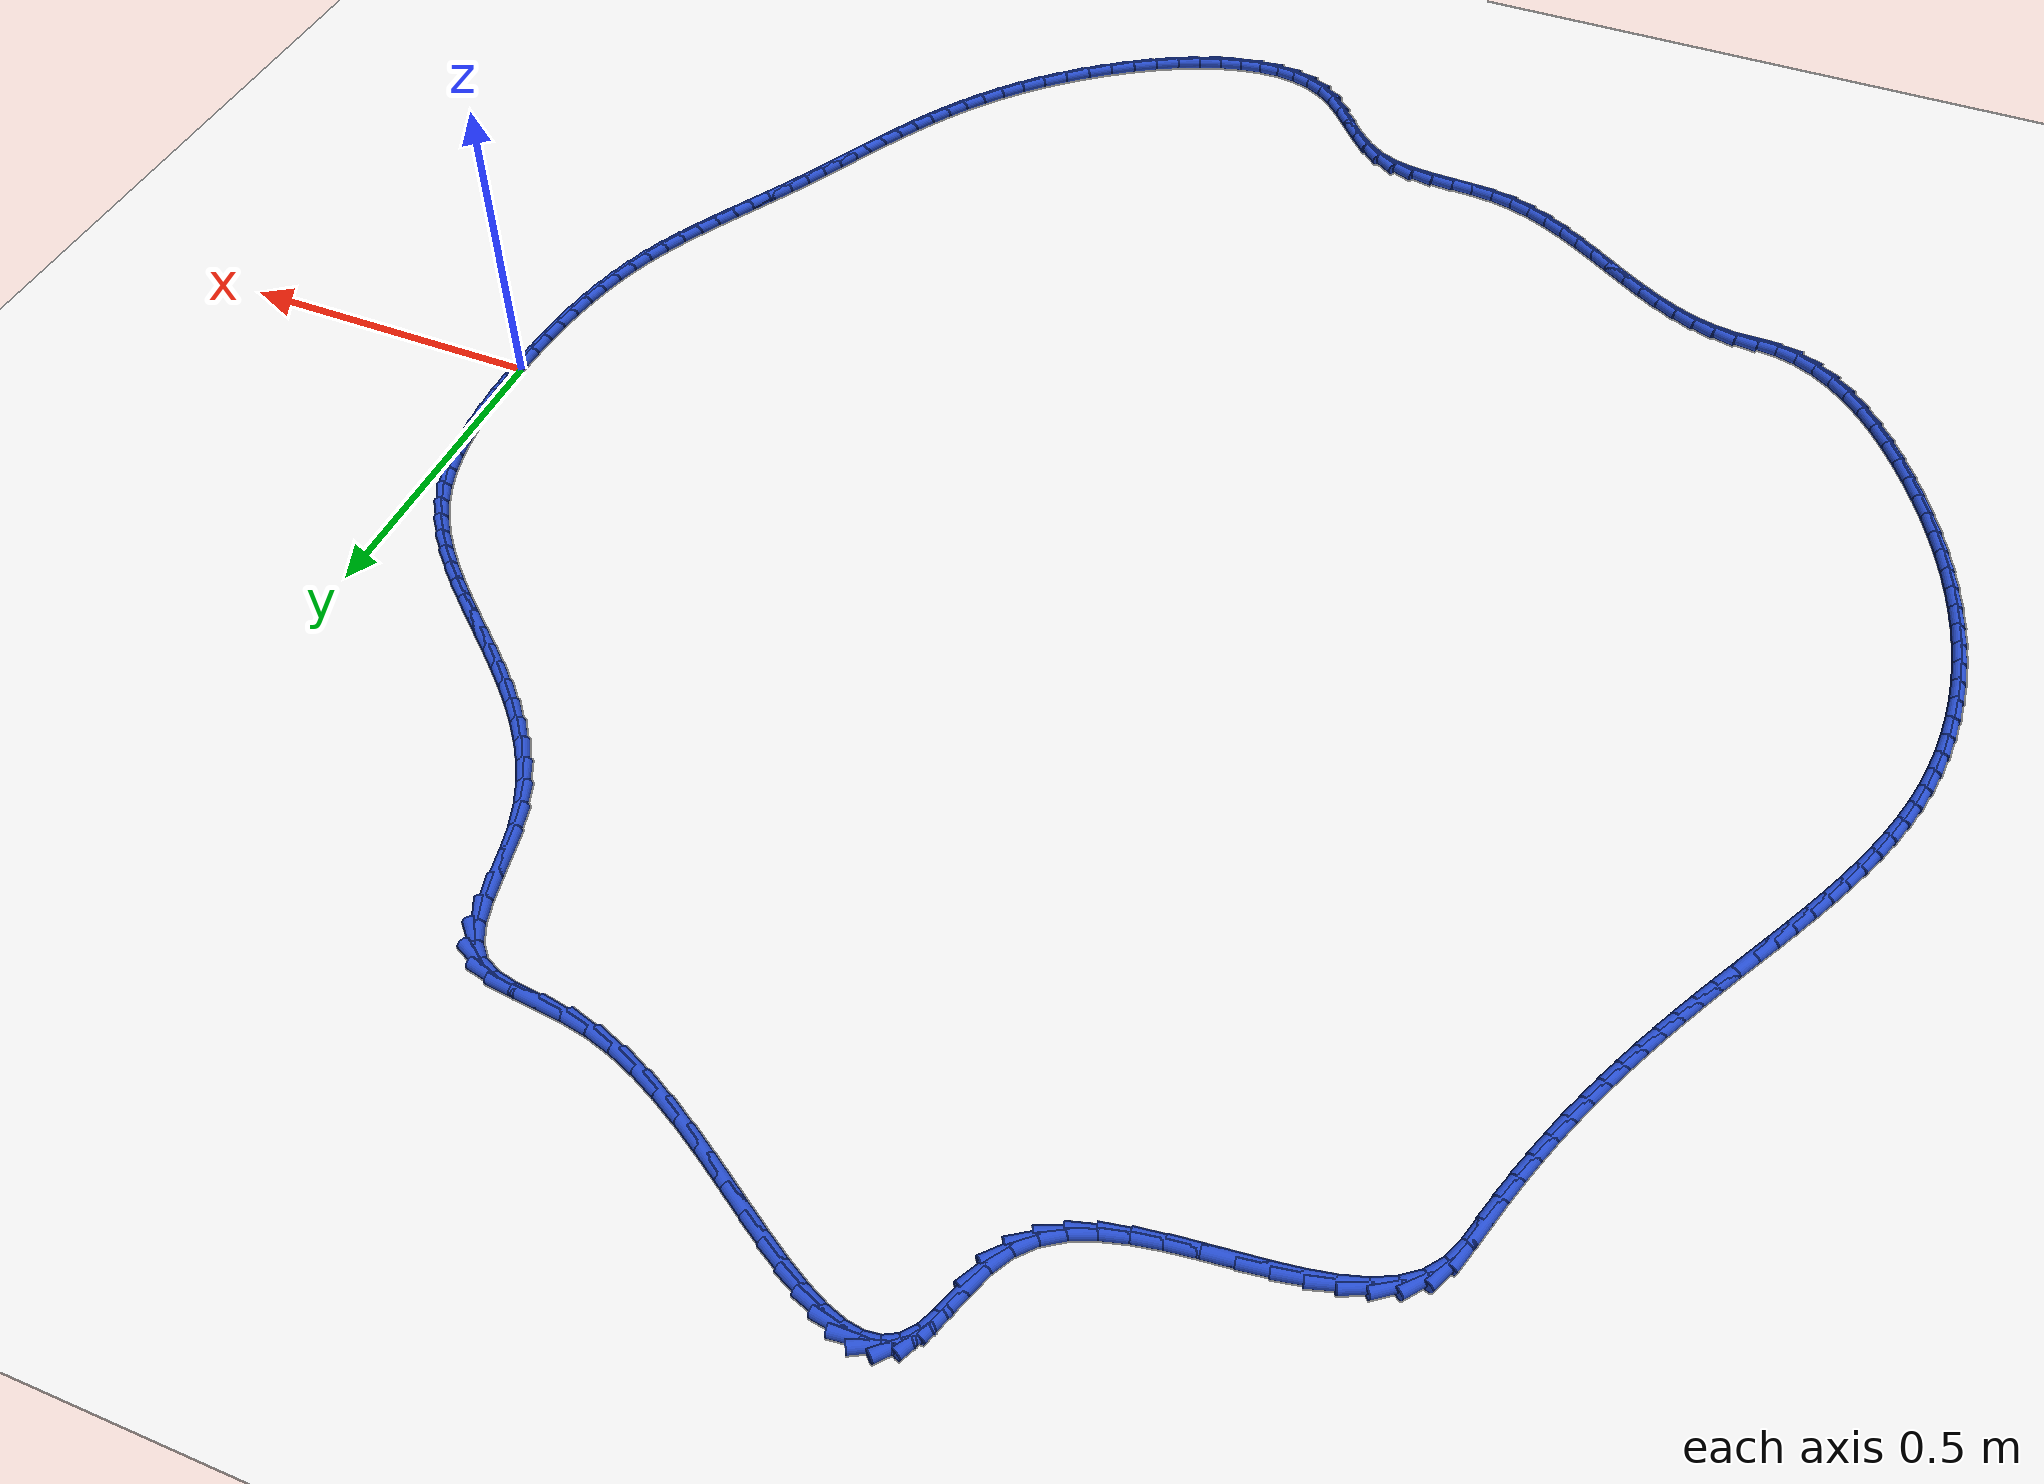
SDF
<sdf version="1.6">
 <world name="default">
  <light name="sun" type="directional">
   <pose>0 0 10 0 -0 0</pose>
   <diffuse>0.8 0.8 0.8 1</diffuse>
   <specular>0.2 0.2 0.2 1</specular>
   <attenuation>
    <range>1000</range>
    <constant>0.9</constant>
    <linear>0.01</linear>
    <quadratic>0.001</quadratic>
   </attenuation>
   <direction>-0.5 0.1 -0.9</direction>
  </light>
  <model name="ground_plane">
   <static>1</static>
   <link name="link">
    <collision name="collision">
     <geometry><plane><normal>0 0 1</normal><size>100 100</size></plane></geometry>
     <surface><friction><ode><mu>100</mu><mu2>50</mu2></ode></friction></surface>
    </collision>
    <visual name="visual">
     <cast_shadows>0</cast_shadows>
     <geometry><plane><normal>0 0 1</normal><size>100 100</size></plane></geometry>
     <material>
      <script><uri>file://media/materials/scripts/gazebo.material</uri><name>Gazebo/WhiteGlow</name></script>
     </material>
    </visual>
   </link>
  </model>
  <gravity>0 0 -9.8</gravity>
  <magnetic_field>6e-06 2.3e-05 -4.2e-05</magnetic_field>
  <atmosphere type="adiabatic"/>
  <physics name="default_physics" default="0" type="ode">
   <max_step_size>0.001</max_step_size>
   <real_time_factor>1</real_time_factor>
   <real_time_update_rate>1000</real_time_update_rate>
  </physics>
  <scene><ambient>0.4 0.4 0.4 1</ambient><background>0.7 0.7 0.7 1</background><shadows>1</shadows></scene>
  <spherical_coordinates>
   <surface_model>EARTH_WGS84</surface_model>
   <latitude_deg>0</latitude_deg>
   <longitude_deg>0</longitude_deg>
   <elevation>0</elevation>
   <heading_deg>0</heading_deg>
  </spherical_coordinates>
  <model name="line">
   <link name="link_0">
    <pose>-1.0842021724855044e-17 -6.938893903907228e-18 0.01 0 1.57 1.5599165693631913</pose>
    <collision name="collision">
     <geometry><cylinder><radius>0.01</radius><length>0.08</length></cylinder></geometry>
    </collision>
    <visual name="visual">
     <material>
      <script><name>Gazebo/Blue</name><uri>file://media/materials/scripts/gazebo.material</uri></script>
     </material>
     <geometry><cylinder><radius>0.01</radius><length>0.08</length></cylinder></geometry>
    </visual>
   </link>
   <link name="link_1">
    <pose>0.0004083220893479926 0.037528959710256535 0.01 0 1.57 -1.5551008602522687</pose>
    <collision name="collision">
     <geometry><cylinder><radius>0.01</radius><length>0.08</length></cylinder></geometry>
    </collision>
    <visual name="visual">
     <material>
      <script><name>Gazebo/Blue</name><uri>file://media/materials/scripts/gazebo.material</uri></script>
     </material>
     <geometry><cylinder><radius>0.01</radius><length>0.08</length></cylinder></geometry>
    </visual>
   </link>
   <link name="link_2">
    <pose>-0.00018199198772292239 0.07513635420890721 0.01 0 1.57 -1.5213480015440761</pose>
    <collision name="collision">
     <geometry><cylinder><radius>0.01</radius><length>0.08</length></cylinder></geometry>
    </collision>
    <visual name="visual">
     <material>
      <script><name>Gazebo/Blue</name><uri>file://media/materials/scripts/gazebo.material</uri></script>
     </material>
     <geometry><cylinder><radius>0.01</radius><length>0.08</length></cylinder></geometry>
    </visual>
   </link>
   <link name="link_3">
    <pose>-0.0020345984019626466 0.11257131686752371 0.01 0 1.57 -1.479765093921134</pose>
    <collision name="collision">
     <geometry><cylinder><radius>0.01</radius><length>0.08</length></cylinder></geometry>
    </collision>
    <visual name="visual">
     <material>
      <script><name>Gazebo/Blue</name><uri>file://media/materials/scripts/gazebo.material</uri></script>
     </material>
     <geometry><cylinder><radius>0.01</radius><length>0.08</length></cylinder></geometry>
    </visual>
   </link>
   <link name="link_4">
    <pose>-0.0054131533241210785 0.14958298105767795 0.01 0 1.57 -1.4295172410705077</pose>
    <collision name="collision">
     <geometry><cylinder><radius>0.01</radius><length>0.08</length></cylinder></geometry>
    </collision>
    <visual name="visual">
     <material>
      <script><name>Gazebo/Blue</name><uri>file://media/materials/scripts/gazebo.material</uri></script>
     </material>
     <geometry><cylinder><radius>0.01</radius><length>0.08</length></cylinder></geometry>
    </visual>
   </link>
   <link name="link_5">
    <pose>-0.010581312924948105 0.18592048015094145 0.01 0 1.57 -1.3696314081925747</pose>
    <collision name="collision">
     <geometry><cylinder><radius>0.01</radius><length>0.08</length></cylinder></geometry>
    </collision>
    <visual name="visual">
     <material>
      <script><name>Gazebo/Blue</name><uri>file://media/materials/scripts/gazebo.material</uri></script>
     </material>
     <geometry><cylinder><radius>0.01</radius><length>0.08</length></cylinder></geometry>
    </visual>
   </link>
   <link name="link_6">
    <pose>-0.017802733375193613 0.22133294751888621 0.01 0 1.57 -1.2990855193037376</pose>
    <collision name="collision">
     <geometry><cylinder><radius>0.01</radius><length>0.08</length></cylinder></geometry>
    </collision>
    <visual name="visual">
     <material>
      <script><name>Gazebo/Blue</name><uri>file://media/materials/scripts/gazebo.material</uri></script>
     </material>
     <geometry><cylinder><radius>0.01</radius><length>0.08</length></cylinder></geometry>
    </visual>
   </link>
   <link name="link_7">
    <pose>-0.027341070845607517 0.25556951653308385 0.01 0 1.57 -1.2169719109412405</pose>
    <collision name="collision">
     <geometry><cylinder><radius>0.01</radius><length>0.08</length></cylinder></geometry>
    </collision>
    <visual name="visual">
     <material>
      <script><name>Gazebo/Blue</name><uri>file://media/materials/scripts/gazebo.material</uri></script>
     </material>
     <geometry><cylinder><radius>0.01</radius><length>0.08</length></cylinder></geometry>
    </visual>
   </link>
   <link name="link_8">
    <pose>-0.03945998150693969 0.28837932056510623 0.01 0 1.57 -1.122912732611828</pose>
    <collision name="collision">
     <geometry><cylinder><radius>0.01</radius><length>0.08</length></cylinder></geometry>
    </collision>
    <visual name="visual">
     <material>
      <script><name>Gazebo/Blue</name><uri>file://media/materials/scripts/gazebo.material</uri></script>
     </material>
     <geometry><cylinder><radius>0.01</radius><length>0.08</length></cylinder></geometry>
    </visual>
   </link>
   <link name="link_9">
    <pose>-0.0544189589920853 0.31951483123892943 0.01 0 1.57 -1.0257252138878534</pose>
    <collision name="collision">
     <geometry><cylinder><radius>0.01</radius><length>0.08</length></cylinder></geometry>
    </collision>
    <visual name="visual">
     <material>
      <script><name>Gazebo/Blue</name><uri>file://media/materials/scripts/gazebo.material</uri></script>
     </material>
     <geometry><cylinder><radius>0.01</radius><length>0.08</length></cylinder></geometry>
    </visual>
   </link>
   <link name="link_10">
    <pose>-0.07224537632955454 0.3489146751620366 0.01 0 1.57 -0.9398377868183616</pose>
    <collision name="collision">
     <geometry><cylinder><radius>0.01</radius><length>0.08</length></cylinder></geometry>
    </collision>
    <visual name="visual">
     <material>
      <script><name>Gazebo/Blue</name><uri>file://media/materials/scripts/gazebo.material</uri></script>
     </material>
     <geometry><cylinder><radius>0.01</radius><length>0.08</length></cylinder></geometry>
    </visual>
   </link>
   <link name="link_11">
    <pose>-0.09261660742854755 0.37679816957881124 0.01 0 1.57 -0.8674778385324577</pose>
    <collision name="collision">
     <geometry><cylinder><radius>0.01</radius><length>0.08</length></cylinder></geometry>
    </collision>
    <visual name="visual">
     <material>
      <script><name>Gazebo/Blue</name><uri>file://media/materials/scripts/gazebo.material</uri></script>
     </material>
     <geometry><cylinder><radius>0.01</radius><length>0.08</length></cylinder></geometry>
    </visual>
   </link>
   <link name="link_12">
    <pose>-0.11518103435650628 0.4034078824736506 0.01 0 1.57 -0.8088510228906319</pose>
    <collision name="collision">
     <geometry><cylinder><radius>0.01</radius><length>0.08</length></cylinder></geometry>
    </collision>
    <visual name="visual">
     <material>
      <script><name>Gazebo/Blue</name><uri>file://media/materials/scripts/gazebo.material</uri></script>
     </material>
     <geometry><cylinder><radius>0.01</radius><length>0.08</length></cylinder></geometry>
    </visual>
   </link>
   <link name="link_13">
    <pose>-0.13958703918087262 0.42898638183095195 0.01 0 1.57 -0.763578737884439</pose>
    <collision name="collision">
     <geometry><cylinder><radius>0.01</radius><length>0.08</length></cylinder></geometry>
    </collision>
    <visual name="visual">
     <material>
      <script><name>Gazebo/Blue</name><uri>file://media/materials/scripts/gazebo.material</uri></script>
     </material>
     <geometry><cylinder><radius>0.01</radius><length>0.08</length></cylinder></geometry>
    </visual>
   </link>
   <link name="link_14">
    <pose>-0.16548300396908855 0.45377623563511243 0.01 0 1.57 -0.731032231703578</pose>
    <collision name="collision">
     <geometry><cylinder><radius>0.01</radius><length>0.08</length></cylinder></geometry>
    </collision>
    <visual name="visual">
     <material>
      <script><name>Gazebo/Blue</name><uri>file://media/materials/scripts/gazebo.material</uri></script>
     </material>
     <geometry><cylinder><radius>0.01</radius><length>0.08</length></cylinder></geometry>
    </visual>
   </link>
   <link name="link_15">
    <pose>-0.19251731078859585 0.47802001187052917 0.01 0 1.57 -0.7105639254891665</pose>
    <collision name="collision">
     <geometry><cylinder><radius>0.01</radius><length>0.08</length></cylinder></geometry>
    </collision>
    <visual name="visual">
     <material>
      <script><name>Gazebo/Blue</name><uri>file://media/materials/scripts/gazebo.material</uri></script>
     </material>
     <geometry><cylinder><radius>0.01</radius><length>0.08</length></cylinder></geometry>
    </visual>
   </link>
   <link name="link_16">
    <pose>-0.22033834170683653 0.5019602785215994 0.01 0 1.57 -0.7016437874296276</pose>
    <collision name="collision">
     <geometry><cylinder><radius>0.01</radius><length>0.08</length></cylinder></geometry>
    </collision>
    <visual name="visual">
     <material>
      <script><name>Gazebo/Blue</name><uri>file://media/materials/scripts/gazebo.material</uri></script>
     </material>
     <geometry><cylinder><radius>0.01</radius><length>0.08</length></cylinder></geometry>
    </visual>
   </link>
   <link name="link_17">
    <pose>-0.24859447879125263 0.5258396035727206 0.01 0 1.57 -0.7039257250999026</pose>
    <collision name="collision">
     <geometry><cylinder><radius>0.01</radius><length>0.08</length></cylinder></geometry>
    </collision>
    <visual name="visual">
     <material>
      <script><name>Gazebo/Blue</name><uri>file://media/materials/scripts/gazebo.material</uri></script>
     </material>
     <geometry><cylinder><radius>0.01</radius><length>0.08</length></cylinder></geometry>
    </visual>
   </link>
   <link name="link_18">
    <pose>-0.27693410410928565 0.5499005550082894 0.01 0 1.57 -0.7172659782463904</pose>
    <collision name="collision">
     <geometry><cylinder><radius>0.01</radius><length>0.08</length></cylinder></geometry>
    </collision>
    <visual name="visual">
     <material>
      <script><name>Gazebo/Blue</name><uri>file://media/materials/scripts/gazebo.material</uri></script>
     </material>
     <geometry><cylinder><radius>0.01</radius><length>0.08</length></cylinder></geometry>
    </visual>
   </link>
   <link name="link_19">
    <pose>-0.30500559972837804 0.5743857008127036 0.01 0 1.57 -0.7417058360498545</pose>
    <collision name="collision">
     <geometry><cylinder><radius>0.01</radius><length>0.08</length></cylinder></geometry>
    </collision>
    <visual name="visual">
     <material>
      <script><name>Gazebo/Blue</name><uri>file://media/materials/scripts/gazebo.material</uri></script>
     </material>
     <geometry><cylinder><radius>0.01</radius><length>0.08</length></cylinder></geometry>
    </visual>
   </link>
   <link name="link_20">
    <pose>-0.3324573477159713 0.59953760897036 0.01 0 1.57 -0.7774209630364739</pose>
    <collision name="collision">
     <geometry><cylinder><radius>0.01</radius><length>0.08</length></cylinder></geometry>
    </collision>
    <visual name="visual">
     <material>
      <script><name>Gazebo/Blue</name><uri>file://media/materials/scripts/gazebo.material</uri></script>
     </material>
     <geometry><cylinder><radius>0.01</radius><length>0.08</length></cylinder></geometry>
    </visual>
   </link>
   <link name="link_21">
    <pose>-0.3589377301395075 0.625598847465656 0.01 0 1.57 -0.8246317318995979</pose>
    <collision name="collision">
     <geometry><cylinder><radius>0.01</radius><length>0.08</length></cylinder></geometry>
    </collision>
    <visual name="visual">
     <material>
      <script><name>Gazebo/Blue</name><uri>file://media/materials/scripts/gazebo.material</uri></script>
     </material>
     <geometry><cylinder><radius>0.01</radius><length>0.08</length></cylinder></geometry>
    </visual>
   </link>
   <link name="link_22">
    <pose>-0.3840951290664286 0.6528119842829887 0.01 0 1.57 -0.8834654898350305</pose>
    <collision name="collision">
     <geometry><cylinder><radius>0.01</radius><length>0.08</length></cylinder></geometry>
    </collision>
    <visual name="visual">
     <material>
      <script><name>Gazebo/Blue</name><uri>file://media/materials/scripts/gazebo.material</uri></script>
     </material>
     <geometry><cylinder><radius>0.01</radius><length>0.08</length></cylinder></geometry>
    </visual>
   </link>
   <link name="link_23">
    <pose>-0.40757792656417646 0.6814195874067552 0.01 0 1.57 -0.9537667515813676</pose>
    <collision name="collision">
     <geometry><cylinder><radius>0.01</radius><length>0.08</length></cylinder></geometry>
    </collision>
    <visual name="visual">
     <material>
      <script><name>Gazebo/Blue</name><uri>file://media/materials/scripts/gazebo.material</uri></script>
     </material>
     <geometry><cylinder><radius>0.01</radius><length>0.08</length></cylinder></geometry>
    </visual>
   </link>
   <link name="link_24">
    <pose>-0.429034504700193 0.7116642248213529 0.01 0 1.57 -1.0348706292430576</pose>
    <collision name="collision">
     <geometry><cylinder><radius>0.01</radius><length>0.08</length></cylinder></geometry>
    </collision>
    <visual name="visual">
     <material>
      <script><name>Gazebo/Blue</name><uri>file://media/materials/scripts/gazebo.material</uri></script>
     </material>
     <geometry><cylinder><radius>0.01</radius><length>0.08</length></cylinder></geometry>
    </visual>
   </link>
   <link name="link_25">
    <pose>-0.4481132455419201 0.7437884645111792 0.01 0 1.57 -1.1253904507145251</pose>
    <collision name="collision">
     <geometry><cylinder><radius>0.01</radius><length>0.08</length></cylinder></geometry>
    </collision>
    <visual name="visual">
     <material>
      <script><name>Gazebo/Blue</name><uri>file://media/materials/scripts/gazebo.material</uri></script>
     </material>
     <geometry><cylinder><radius>0.01</radius><length>0.08</length></cylinder></geometry>
    </visual>
   </link>
   <link name="link_26">
    <pose>-0.4644625311567998 0.778034874460631 0.01 0 1.57 -1.2231097033588787</pose>
    <collision name="collision">
     <geometry><cylinder><radius>0.01</radius><length>0.08</length></cylinder></geometry>
    </collision>
    <visual name="visual">
     <material>
      <script><name>Gazebo/Blue</name><uri>file://media/materials/scripts/gazebo.material</uri></script>
     </material>
     <geometry><cylinder><radius>0.01</radius><length>0.08</length></cylinder></geometry>
    </visual>
   </link>
   <link name="link_27">
    <pose>-0.47773074361227374 0.8146460226541054 0.01 0 1.57 -1.3179754953305867</pose>
    <collision name="collision">
     <geometry><cylinder><radius>0.01</radius><length>0.08</length></cylinder></geometry>
    </collision>
    <visual name="visual">
     <material>
      <script><name>Gazebo/Blue</name><uri>file://media/materials/scripts/gazebo.material</uri></script>
     </material>
     <geometry><cylinder><radius>0.01</radius><length>0.08</length></cylinder></geometry>
    </visual>
   </link>
   <link name="link_28">
    <pose>-0.4877997644193613 0.8536205374214973 0.01 0 1.57 -1.3667069288833278</pose>
    <collision name="collision">
     <geometry><cylinder><radius>0.01</radius><length>0.08</length></cylinder></geometry>
    </collision>
    <visual name="visual">
     <material>
      <script><name>Gazebo/Blue</name><uri>file://media/materials/scripts/gazebo.material</uri></script>
     </material>
     <geometry><cylinder><radius>0.01</radius><length>0.08</length></cylinder></geometry>
    </visual>
   </link>
   <link name="link_29">
    <pose>-0.49603454696372246 0.8934076642112743 0.01 0 1.57 -1.3570143810669486</pose>
    <collision name="collision">
     <geometry><cylinder><radius>0.01</radius><length>0.08</length></cylinder></geometry>
    </collision>
    <visual name="visual">
     <material>
      <script><name>Gazebo/Blue</name><uri>file://media/materials/scripts/gazebo.material</uri></script>
     </material>
     <geometry><cylinder><radius>0.01</radius><length>0.08</length></cylinder></geometry>
    </visual>
   </link>
   <link name="link_30">
    <pose>-0.5043804246000214 0.9318503185939813 0.01 0 1.57 -1.2813955251912204</pose>
    <collision name="collision">
     <geometry><cylinder><radius>0.01</radius><length>0.08</length></cylinder></geometry>
    </collision>
    <visual name="visual">
     <material>
      <script><name>Gazebo/Blue</name><uri>file://media/materials/scripts/gazebo.material</uri></script>
     </material>
     <geometry><cylinder><radius>0.01</radius><length>0.08</length></cylinder></geometry>
    </visual>
   </link>
   <link name="link_31">
    <pose>-0.5147840785955787 0.9667900079597309 0.01 0 1.57 -1.1134805893853406</pose>
    <collision name="collision">
     <geometry><cylinder><radius>0.01</radius><length>0.08</length></cylinder></geometry>
    </collision>
    <visual name="visual">
     <material>
      <script><name>Gazebo/Blue</name><uri>file://media/materials/scripts/gazebo.material</uri></script>
     </material>
     <geometry><cylinder><radius>0.01</radius><length>0.08</length></cylinder></geometry>
    </visual>
   </link>
   <link name="link_32">
    <pose>-0.5291921902177145 0.9960682396986354 0.01 0 1.57 -0.8118911979268411</pose>
    <collision name="collision">
     <geometry><cylinder><radius>0.01</radius><length>0.08</length></cylinder></geometry>
    </collision>
    <visual name="visual">
     <material>
      <script><name>Gazebo/Blue</name><uri>file://media/materials/scripts/gazebo.material</uri></script>
     </material>
     <geometry><cylinder><radius>0.01</radius><length>0.08</length></cylinder></geometry>
    </visual>
   </link>
   <link name="link_33">
    <pose>-0.5495478442204685 1.0175320782448027 0.01 0 1.57 -0.44181427309850313</pose>
    <collision name="collision">
     <geometry><cylinder><radius>0.01</radius><length>0.08</length></cylinder></geometry>
    </collision>
    <visual name="visual">
     <material>
      <script><name>Gazebo/Blue</name><uri>file://media/materials/scripts/gazebo.material</uri></script>
     </material>
     <geometry><cylinder><radius>0.01</radius><length>0.08</length></cylinder></geometry>
    </visual>
   </link>
   <link name="link_34">
    <pose>-0.5768705189167372 1.0304556706613401 0.01 0 1.57 -0.2072579754254557</pose>
    <collision name="collision">
     <geometry><cylinder><radius>0.01</radius><length>0.08</length></cylinder></geometry>
    </collision>
    <visual name="visual">
     <material>
      <script><name>Gazebo/Blue</name><uri>file://media/materials/scripts/gazebo.material</uri></script>
     </material>
     <geometry><cylinder><radius>0.01</radius><length>0.08</length></cylinder></geometry>
    </visual>
   </link>
   <link name="link_35">
    <pose>-0.6100336075477354 1.0374291226163637 0.01 0 1.57 -0.10825156294374857</pose>
    <collision name="collision">
     <geometry><cylinder><radius>0.01</radius><length>0.08</length></cylinder></geometry>
    </collision>
    <visual name="visual">
     <material>
      <script><name>Gazebo/Blue</name><uri>file://media/materials/scripts/gazebo.material</uri></script>
     </material>
     <geometry><cylinder><radius>0.01</radius><length>0.08</length></cylinder></geometry>
    </visual>
   </link>
   <link name="link_36">
    <pose>-0.6476064105717211 1.0415123995676463 0.01 0 1.57 -0.1044977878045931</pose>
    <collision name="collision">
     <geometry><cylinder><radius>0.01</radius><length>0.08</length></cylinder></geometry>
    </collision>
    <visual name="visual">
     <material>
      <script><name>Gazebo/Blue</name><uri>file://media/materials/scripts/gazebo.material</uri></script>
     </material>
     <geometry><cylinder><radius>0.01</radius><length>0.08</length></cylinder></geometry>
    </visual>
   </link>
   <link name="link_37">
    <pose>-0.6881582284469525 1.0457654669729637 0.01 0 1.57 -0.17570593819324148</pose>
    <collision name="collision">
     <geometry><cylinder><radius>0.01</radius><length>0.08</length></cylinder></geometry>
    </collision>
    <visual name="visual">
     <material>
      <script><name>Gazebo/Blue</name><uri>file://media/materials/scripts/gazebo.material</uri></script>
     </material>
     <geometry><cylinder><radius>0.01</radius><length>0.08</length></cylinder></geometry>
    </visual>
   </link>
   <link name="link_38">
    <pose>-0.7302607166569515 1.053240204417094 0.01 0 1.57 -0.2864546156416662</pose>
    <collision name="collision">
     <geometry><cylinder><radius>0.01</radius><length>0.08</length></cylinder></geometry>
    </collision>
    <visual name="visual">
     <material>
      <script><name>Gazebo/Blue</name><uri>file://media/materials/scripts/gazebo.material</uri></script>
     </material>
     <geometry><cylinder><radius>0.01</radius><length>0.08</length></cylinder></geometry>
    </visual>
   </link>
   <link name="link_39">
    <pose>-0.7728371190922563 1.0657813285514586 0.01 0 1.57 -0.3783870833584046</pose>
    <collision name="collision">
     <geometry><cylinder><radius>0.01</radius><length>0.08</length></cylinder></geometry>
    </collision>
    <visual name="visual">
     <material>
      <script><name>Gazebo/Blue</name><uri>file://media/materials/scripts/gazebo.material</uri></script>
     </material>
     <geometry><cylinder><radius>0.01</radius><length>0.08</length></cylinder></geometry>
    </visual>
   </link>
   <link name="link_40">
    <pose>-0.8155326592903765 1.0827546714821707 0.01 0 1.57 -0.44835178662146985</pose>
    <collision name="collision">
     <geometry><cylinder><radius>0.01</radius><length>0.08</length></cylinder></geometry>
    </collision>
    <visual name="visual">
     <material>
      <script><name>Gazebo/Blue</name><uri>file://media/materials/scripts/gazebo.material</uri></script>
     </material>
     <geometry><cylinder><radius>0.01</radius><length>0.08</length></cylinder></geometry>
    </visual>
   </link>
   <link name="link_41">
    <pose>-0.8580812488932248 1.1032215587100955 0.01 0 1.57 -0.5000548467181876</pose>
    <collision name="collision">
     <geometry><cylinder><radius>0.01</radius><length>0.08</length></cylinder></geometry>
    </collision>
    <visual name="visual">
     <material>
      <script><name>Gazebo/Blue</name><uri>file://media/materials/scripts/gazebo.material</uri></script>
     </material>
     <geometry><cylinder><radius>0.01</radius><length>0.08</length></cylinder></geometry>
    </visual>
   </link>
   <link name="link_42">
    <pose>-0.9002167995427136 1.1262433157360994 0.01 0 1.57 -0.5362249115061972</pose>
    <collision name="collision">
     <geometry><cylinder><radius>0.01</radius><length>0.08</length></cylinder></geometry>
    </collision>
    <visual name="visual">
     <material>
      <script><name>Gazebo/Blue</name><uri>file://media/materials/scripts/gazebo.material</uri></script>
     </material>
     <geometry><cylinder><radius>0.01</radius><length>0.08</length></cylinder></geometry>
    </visual>
   </link>
   <link name="link_43">
    <pose>-0.9416732228807557 1.1508812680610478 0.01 0 1.57 -0.5585277473288536</pose>
    <collision name="collision">
     <geometry><cylinder><radius>0.01</radius><length>0.08</length></cylinder></geometry>
    </collision>
    <visual name="visual">
     <material>
      <script><name>Gazebo/Blue</name><uri>file://media/materials/scripts/gazebo.material</uri></script>
     </material>
     <geometry><cylinder><radius>0.01</radius><length>0.08</length></cylinder></geometry>
    </visual>
   </link>
   <link name="link_44">
    <pose>-0.9821844305492633 1.1761967411858063 0.01 0 1.57 -0.5675490384119425</pose>
    <collision name="collision">
     <geometry><cylinder><radius>0.01</radius><length>0.08</length></cylinder></geometry>
    </collision>
    <visual name="visual">
     <material>
      <script><name>Gazebo/Blue</name><uri>file://media/materials/scripts/gazebo.material</uri></script>
     </material>
     <geometry><cylinder><radius>0.01</radius><length>0.08</length></cylinder></geometry>
    </visual>
   </link>
   <link name="link_45">
    <pose>-1.0214843341901496 1.2012510606112419 0.01 0 1.57 -0.5626845436262138</pose>
    <collision name="collision">
     <geometry><cylinder><radius>0.01</radius><length>0.08</length></cylinder></geometry>
    </collision>
    <visual name="visual">
     <material>
      <script><name>Gazebo/Blue</name><uri>file://media/materials/scripts/gazebo.material</uri></script>
     </material>
     <geometry><cylinder><radius>0.01</radius><length>0.08</length></cylinder></geometry>
    </visual>
   </link>
   <link name="link_46">
    <pose>-1.0593068454453263 1.2251055518382195 0.01 0 1.57 -0.5418157963368851</pose>
    <collision name="collision">
     <geometry><cylinder><radius>0.01</radius><length>0.08</length></cylinder></geometry>
    </collision>
    <visual name="visual">
     <material>
      <script><name>Gazebo/Blue</name><uri>file://media/materials/scripts/gazebo.material</uri></script>
     </material>
     <geometry><cylinder><radius>0.01</radius><length>0.08</length></cylinder></geometry>
    </visual>
   </link>
   <link name="link_47">
    <pose>-1.0953858759567063 1.2468215403676046 0.01 0 1.57 -0.5006006462898879</pose>
    <collision name="collision">
     <geometry><cylinder><radius>0.01</radius><length>0.08</length></cylinder></geometry>
    </collision>
    <visual name="visual">
     <material>
      <script><name>Gazebo/Blue</name><uri>file://media/materials/scripts/gazebo.material</uri></script>
     </material>
     <geometry><cylinder><radius>0.01</radius><length>0.08</length></cylinder></geometry>
    </visual>
   </link>
   <link name="link_48">
    <pose>-1.1294553373662017 1.2654603517002636 0.01 0 1.57 -0.4310818830031879</pose>
    <collision name="collision">
     <geometry><cylinder><radius>0.01</radius><length>0.08</length></cylinder></geometry>
    </collision>
    <visual name="visual">
     <material>
      <script><name>Gazebo/Blue</name><uri>file://media/materials/scripts/gazebo.material</uri></script>
     </material>
     <geometry><cylinder><radius>0.01</radius><length>0.08</length></cylinder></geometry>
    </visual>
   </link>
   <link name="link_49">
    <pose>-1.1612491413157264 1.280083311337063 0.01 0 1.57 -0.31921775201873503</pose>
    <collision name="collision">
     <geometry><cylinder><radius>0.01</radius><length>0.08</length></cylinder></geometry>
    </collision>
    <visual name="visual">
     <material>
      <script><name>Gazebo/Blue</name><uri>file://media/materials/scripts/gazebo.material</uri></script>
     </material>
     <geometry><cylinder><radius>0.01</radius><length>0.08</length></cylinder></geometry>
    </visual>
   </link>
   <link name="link_50">
    <pose>-1.190501199447192 1.2897517447788676 0.01 0 1.57 -0.14180390406216242</pose>
    <collision name="collision">
     <geometry><cylinder><radius>0.01</radius><length>0.08</length></cylinder></geometry>
    </collision>
    <visual name="visual">
     <material>
      <script><name>Gazebo/Blue</name><uri>file://media/materials/scripts/gazebo.material</uri></script>
     </material>
     <geometry><cylinder><radius>0.01</radius><length>0.08</length></cylinder></geometry>
    </visual>
   </link>
   <link name="link_51">
    <pose>-1.2169454234025103 1.2935269775265434 0.01 0 1.57 0.13005350951575115</pose>
    <collision name="collision">
     <geometry><cylinder><radius>0.01</radius><length>0.08</length></cylinder></geometry>
    </collision>
    <visual name="visual">
     <material>
      <script><name>Gazebo/Blue</name><uri>file://media/materials/scripts/gazebo.material</uri></script>
     </material>
     <geometry><cylinder><radius>0.01</radius><length>0.08</length></cylinder></geometry>
    </visual>
   </link>
   <link name="link_52">
    <pose>-1.2403157248235954 1.290470335080957 0.01 0 1.57 0.49555198521306687</pose>
    <collision name="collision">
     <geometry><cylinder><radius>0.01</radius><length>0.08</length></cylinder></geometry>
    </collision>
    <visual name="visual">
     <material>
      <script><name>Gazebo/Blue</name><uri>file://media/materials/scripts/gazebo.material</uri></script>
     </material>
     <geometry><cylinder><radius>0.01</radius><length>0.08</length></cylinder></geometry>
    </visual>
   </link>
   <link name="link_53">
    <pose>-1.2603460153523587 1.279643142942973 0.01 0 1.57 0.8717284479491614</pose>
    <collision name="collision">
     <geometry><cylinder><radius>0.01</radius><length>0.08</length></cylinder></geometry>
    </collision>
    <visual name="visual">
     <material>
      <script><name>Gazebo/Blue</name><uri>file://media/materials/scripts/gazebo.material</uri></script>
     </material>
     <geometry><cylinder><radius>0.01</radius><length>0.08</length></cylinder></geometry>
    </visual>
   </link>
   <link name="link_54">
    <pose>-1.2767702066307134 1.2601067266134585 0.01 0 1.57 1.1521482262837601</pose>
    <collision name="collision">
     <geometry><cylinder><radius>0.01</radius><length>0.08</length></cylinder></geometry>
    </collision>
    <visual name="visual">
     <material>
      <script><name>Gazebo/Blue</name><uri>file://media/materials/scripts/gazebo.material</uri></script>
     </material>
     <geometry><cylinder><radius>0.01</radius><length>0.08</length></cylinder></geometry>
    </visual>
   </link>
   <link name="link_55">
    <pose>-1.2895647042770406 1.2313519460876943 0.01 0 1.57 1.2603500687234017</pose>
    <collision name="collision">
     <geometry><cylinder><radius>0.01</radius><length>0.08</length></cylinder></geometry>
    </collision>
    <visual name="visual">
     <material>
      <script><name>Gazebo/Blue</name><uri>file://media/materials/scripts/gazebo.material</uri></script>
     </material>
     <geometry><cylinder><radius>0.01</radius><length>0.08</length></cylinder></geometry>
    </visual>
   </link>
   <link name="link_56">
    <pose>-1.300749346286165 1.196489234537456 0.01 0 1.57 1.2340485952930138</pose>
    <collision name="collision">
     <geometry><cylinder><radius>0.01</radius><length>0.08</length></cylinder></geometry>
    </collision>
    <visual name="visual">
     <material>
      <script><name>Gazebo/Blue</name><uri>file://media/materials/scripts/gazebo.material</uri></script>
     </material>
     <geometry><cylinder><radius>0.01</radius><length>0.08</length></cylinder></geometry>
    </visual>
   </link>
   <link name="link_57">
    <pose>-1.313368315069187 1.1604434671563764 0.01 0 1.57 1.0842727911966776</pose>
    <collision name="collision">
     <geometry><cylinder><radius>0.01</radius><length>0.08</length></cylinder></geometry>
    </collision>
    <visual name="visual">
     <material>
      <script><name>Gazebo/Blue</name><uri>file://media/materials/scripts/gazebo.material</uri></script>
     </material>
     <geometry><cylinder><radius>0.01</radius><length>0.08</length></cylinder></geometry>
    </visual>
   </link>
   <link name="link_58">
    <pose>-1.3304590224876394 1.1281316688789473 0.01 0 1.57 0.834133887277974</pose>
    <collision name="collision">
     <geometry><cylinder><radius>0.01</radius><length>0.08</length></cylinder></geometry>
    </collision>
    <visual name="visual">
     <material>
      <script><name>Gazebo/Blue</name><uri>file://media/materials/scripts/gazebo.material</uri></script>
     </material>
     <geometry><cylinder><radius>0.01</radius><length>0.08</length></cylinder></geometry>
    </visual>
   </link>
   <link name="link_59">
    <pose>-1.3537207361879966 1.1024844541929182 0.01 0 1.57 0.5991897227936704</pose>
    <collision name="collision">
     <geometry><cylinder><radius>0.01</radius><length>0.08</length></cylinder></geometry>
    </collision>
    <visual name="visual">
     <material>
      <script><name>Gazebo/Blue</name><uri>file://media/materials/scripts/gazebo.material</uri></script>
     </material>
     <geometry><cylinder><radius>0.01</radius><length>0.08</length></cylinder></geometry>
    </visual>
   </link>
   <link name="link_60">
    <pose>-1.3824491475311054 1.082864444697401 0.01 0 1.57 0.4139201853309544</pose>
    <collision name="collision">
     <geometry><cylinder><radius>0.01</radius><length>0.08</length></cylinder></geometry>
    </collision>
    <visual name="visual">
     <material>
      <script><name>Gazebo/Blue</name><uri>file://media/materials/scripts/gazebo.material</uri></script>
     </material>
     <geometry><cylinder><radius>0.01</radius><length>0.08</length></cylinder></geometry>
    </visual>
   </link>
   <link name="link_61">
    <pose>-1.415689227973836 1.0682620804053544 0.01 0 1.57 0.2803318708007192</pose>
    <collision name="collision">
     <geometry><cylinder><radius>0.01</radius><length>0.08</length></cylinder></geometry>
    </collision>
    <visual name="visual">
     <material>
      <script><name>Gazebo/Blue</name><uri>file://media/materials/scripts/gazebo.material</uri></script>
     </material>
     <geometry><cylinder><radius>0.01</radius><length>0.08</length></cylinder></geometry>
    </visual>
   </link>
   <link name="link_62">
    <pose>-1.452485948973061 1.0576678013297383 0.01 0 1.57 0.19045700513323918</pose>
    <collision name="collision">
     <geometry><cylinder><radius>0.01</radius><length>0.08</length></cylinder></geometry>
    </collision>
    <visual name="visual">
     <material>
      <script><name>Gazebo/Blue</name><uri>file://media/materials/scripts/gazebo.material</uri></script>
     </material>
     <geometry><cylinder><radius>0.01</radius><length>0.08</length></cylinder></geometry>
    </visual>
   </link>
   <link name="link_63">
    <pose>-1.491884281985652 1.0500720474835108 0.01 0 1.57 0.13576102323011224</pose>
    <collision name="collision">
     <geometry><cylinder><radius>0.01</radius><length>0.08</length></cylinder></geometry>
    </collision>
    <visual name="visual">
     <material>
      <script><name>Gazebo/Blue</name><uri>file://media/materials/scripts/gazebo.material</uri></script>
     </material>
     <geometry><cylinder><radius>0.01</radius><length>0.08</length></cylinder></geometry>
    </visual>
   </link>
   <link name="link_64">
    <pose>-1.5329291984684803 1.044465258879632 0.01 0 1.57 0.11042048234627565</pose>
    <collision name="collision">
     <geometry><cylinder><radius>0.01</radius><length>0.08</length></cylinder></geometry>
    </collision>
    <visual name="visual">
     <material>
      <script><name>Gazebo/Blue</name><uri>file://media/materials/scripts/gazebo.material</uri></script>
     </material>
     <geometry><cylinder><radius>0.01</radius><length>0.08</length></cylinder></geometry>
    </visual>
   </link>
   <link name="link_65">
    <pose>-1.5746656698784176 1.0398378755310596 0.01 0 1.57 0.11183432525941048</pose>
    <collision name="collision">
     <geometry><cylinder><radius>0.01</radius><length>0.08</length></cylinder></geometry>
    </collision>
    <visual name="visual">
     <material>
      <script><name>Gazebo/Blue</name><uri>file://media/materials/scripts/gazebo.material</uri></script>
     </material>
     <geometry><cylinder><radius>0.01</radius><length>0.08</length></cylinder></geometry>
    </visual>
   </link>
   <link name="link_66">
    <pose>-1.6161386676723357 1.0351803374507538 0.01 0 1.57 0.14059704245803892</pose>
    <collision name="collision">
     <geometry><cylinder><radius>0.01</radius><length>0.08</length></cylinder></geometry>
    </collision>
    <visual name="visual">
     <material>
      <script><name>Gazebo/Blue</name><uri>file://media/materials/scripts/gazebo.material</uri></script>
     </material>
     <geometry><cylinder><radius>0.01</radius><length>0.08</length></cylinder></geometry>
    </visual>
   </link>
   <link name="link_67">
    <pose>-1.6563931633071056 1.029483084651673 0.01 0 1.57 0.20068430976447896</pose>
    <collision name="collision">
     <geometry><cylinder><radius>0.01</radius><length>0.08</length></cylinder></geometry>
    </collision>
    <visual name="visual">
     <material>
      <script><name>Gazebo/Blue</name><uri>file://media/materials/scripts/gazebo.material</uri></script>
     </material>
     <geometry><cylinder><radius>0.01</radius><length>0.08</length></cylinder></geometry>
    </visual>
   </link>
   <link name="link_68">
    <pose>-1.6944741282395994 1.0217365571467762 0.01 0 1.57 0.29982546258192566</pose>
    <collision name="collision">
     <geometry><cylinder><radius>0.01</radius><length>0.08</length></cylinder></geometry>
    </collision>
    <visual name="visual">
     <material>
      <script><name>Gazebo/Blue</name><uri>file://media/materials/scripts/gazebo.material</uri></script>
     </material>
     <geometry><cylinder><radius>0.01</radius><length>0.08</length></cylinder></geometry>
    </visual>
   </link>
   <link name="link_69">
    <pose>-1.729426533926688 1.0109311949490227 0.01 0 1.57 0.4490123955451565</pose>
    <collision name="collision">
     <geometry><cylinder><radius>0.01</radius><length>0.08</length></cylinder></geometry>
    </collision>
    <visual name="visual">
     <material>
      <script><name>Gazebo/Blue</name><uri>file://media/materials/scripts/gazebo.material</uri></script>
     </material>
     <geometry><cylinder><radius>0.01</radius><length>0.08</length></cylinder></geometry>
    </visual>
   </link>
   <link name="link_70">
    <pose>-1.7602953518252442 0.9960574380713717 0.01 0 1.57 0.657694904254171</pose>
    <collision name="collision">
     <geometry><cylinder><radius>0.01</radius><length>0.08</length></cylinder></geometry>
    </collision>
    <visual name="visual">
     <material>
      <script><name>Gazebo/Blue</name><uri>file://media/materials/scripts/gazebo.material</uri></script>
     </material>
     <geometry><cylinder><radius>0.01</radius><length>0.08</length></cylinder></geometry>
    </visual>
   </link>
   <link name="link_71">
    <pose>-1.786125553392139 0.9761057265267823 0.01 0 1.57 0.9197878578232792</pose>
    <collision name="collision">
     <geometry><cylinder><radius>0.01</radius><length>0.08</length></cylinder></geometry>
    </collision>
    <visual name="visual">
     <material>
      <script><name>Gazebo/Blue</name><uri>file://media/materials/scripts/gazebo.material</uri></script>
     </material>
     <geometry><cylinder><radius>0.01</radius><length>0.08</length></cylinder></geometry>
    </visual>
   </link>
   <link name="link_72">
    <pose>-1.8059621353947113 0.9500665261253635 0.01 0 1.57 1.1695210998663894</pose>
    <collision name="collision">
     <geometry><cylinder><radius>0.01</radius><length>0.08</length></cylinder></geometry>
    </collision>
    <visual name="visual">
     <material>
      <script><name>Gazebo/Blue</name><uri>file://media/materials/scripts/gazebo.material</uri></script>
     </material>
     <geometry><cylinder><radius>0.01</radius><length>0.08</length></cylinder></geometry>
    </visual>
   </link>
   <link name="link_73">
    <pose>-1.819668024144276 0.9177639597984742 0.01 0 1.57 1.2872621960160442</pose>
    <collision name="collision">
     <geometry><cylinder><radius>0.01</radius><length>0.08</length></cylinder></geometry>
    </collision>
    <visual name="visual">
     <material>
      <script><name>Gazebo/Blue</name><uri>file://media/materials/scripts/gazebo.material</uri></script>
     </material>
     <geometry><cylinder><radius>0.01</radius><length>0.08</length></cylinder></geometry>
    </visual>
   </link>
   <link name="link_74">
    <pose>-1.8300750601335252 0.8820481524942884 0.01 0 1.57 1.2924991903023233</pose>
    <collision name="collision">
     <geometry><cylinder><radius>0.01</radius><length>0.08</length></cylinder></geometry>
    </collision>
    <visual name="visual">
     <material>
      <script><name>Gazebo/Blue</name><uri>file://media/materials/scripts/gazebo.material</uri></script>
     </material>
     <geometry><cylinder><radius>0.01</radius><length>0.08</length></cylinder></geometry>
    </visual>
   </link>
   <link name="link_75">
    <pose>-1.840344259426991 0.84610561173369 0.01 0 1.57 1.2680385166494021</pose>
    <collision name="collision">
     <geometry><cylinder><radius>0.01</radius><length>0.08</length></cylinder></geometry>
    </collision>
    <visual name="visual">
     <material>
      <script><name>Gazebo/Blue</name><uri>file://media/materials/scripts/gazebo.material</uri></script>
     </material>
     <geometry><cylinder><radius>0.01</radius><length>0.08</length></cylinder></geometry>
    </visual>
   </link>
   <link name="link_76">
    <pose>-1.8513674132821667 0.8108157704474234 0.01 0 1.57 1.2442187884494504</pose>
    <collision name="collision">
     <geometry><cylinder><radius>0.01</radius><length>0.08</length></cylinder></geometry>
    </collision>
    <visual name="visual">
     <material>
      <script><name>Gazebo/Blue</name><uri>file://media/materials/scripts/gazebo.material</uri></script>
     </material>
     <geometry><cylinder><radius>0.01</radius><length>0.08</length></cylinder></geometry>
    </visual>
   </link>
   <link name="link_77">
    <pose>-1.863117668857513 0.7761240948425848 0.01 0 1.57 1.2212632079221766</pose>
    <collision name="collision">
     <geometry><cylinder><radius>0.01</radius><length>0.08</length></cylinder></geometry>
    </collision>
    <visual name="visual">
     <material>
      <script><name>Gazebo/Blue</name><uri>file://media/materials/scripts/gazebo.material</uri></script>
     </material>
     <geometry><cylinder><radius>0.01</radius><length>0.08</length></cylinder></geometry>
    </visual>
   </link>
   <link name="link_78">
    <pose>-1.8755655760133976 0.7419734105062579 0.01 0 1.57 1.1993004629953616</pose>
    <collision name="collision">
     <geometry><cylinder><radius>0.01</radius><length>0.08</length></cylinder></geometry>
    </collision>
    <visual name="visual">
     <material>
      <script><name>Gazebo/Blue</name><uri>file://media/materials/scripts/gazebo.material</uri></script>
     </material>
     <geometry><cylinder><radius>0.01</radius><length>0.08</length></cylinder></geometry>
    </visual>
   </link>
   <link name="link_79">
    <pose>-1.888681684610185 0.7083065430255263 0.01 0 1.57 1.1784488872686933</pose>
    <collision name="collision">
     <geometry><cylinder><radius>0.01</radius><length>0.08</length></cylinder></geometry>
    </collision>
    <visual name="visual">
     <material>
      <script><name>Gazebo/Blue</name><uri>file://media/materials/scripts/gazebo.material</uri></script>
     </material>
     <geometry><cylinder><radius>0.01</radius><length>0.08</length></cylinder></geometry>
    </visual>
   </link>
   <link name="link_80">
    <pose>-1.902436544508242 0.6750663179874733 0.01 0 1.57 1.158814823958182</pose>
    <collision name="collision">
     <geometry><cylinder><radius>0.01</radius><length>0.08</length></cylinder></geometry>
    </collision>
    <visual name="visual">
     <material>
      <script><name>Gazebo/Blue</name><uri>file://media/materials/scripts/gazebo.material</uri></script>
     </material>
     <geometry><cylinder><radius>0.01</radius><length>0.08</length></cylinder></geometry>
    </visual>
   </link>
   <link name="link_81">
    <pose>-1.9168007055679344 0.6421955609791826 0.01 0 1.57 1.1404914387741663</pose>
    <collision name="collision">
     <geometry><cylinder><radius>0.01</radius><length>0.08</length></cylinder></geometry>
    </collision>
    <visual name="visual">
     <material>
      <script><name>Gazebo/Blue</name><uri>file://media/materials/scripts/gazebo.material</uri></script>
     </material>
     <geometry><cylinder><radius>0.01</radius><length>0.08</length></cylinder></geometry>
    </visual>
   </link>
   <link name="link_82">
    <pose>-1.9317447176496294 0.609637097587738 0.01 0 1.57 1.1235579837236063</pose>
    <collision name="collision">
     <geometry><cylinder><radius>0.01</radius><length>0.08</length></cylinder></geometry>
    </collision>
    <visual name="visual">
     <material>
      <script><name>Gazebo/Blue</name><uri>file://media/materials/scripts/gazebo.material</uri></script>
     </material>
     <geometry><cylinder><radius>0.01</radius><length>0.08</length></cylinder></geometry>
    </visual>
   </link>
   <link name="link_83">
    <pose>-1.947239130613692 0.5773337534002226 0.01 0 1.57 1.1080794860000844</pose>
    <collision name="collision">
     <geometry><cylinder><radius>0.01</radius><length>0.08</length></cylinder></geometry>
    </collision>
    <visual name="visual">
     <material>
      <script><name>Gazebo/Blue</name><uri>file://media/materials/scripts/gazebo.material</uri></script>
     </material>
     <geometry><cylinder><radius>0.01</radius><length>0.08</length></cylinder></geometry>
    </visual>
   </link>
   <link name="link_84">
    <pose>-1.9632544943204893 0.5452283540037209 0.01 0 1.57 1.0941068146139452</pose>
    <collision name="collision">
     <geometry><cylinder><radius>0.01</radius><length>0.08</length></cylinder></geometry>
    </collision>
    <visual name="visual">
     <material>
      <script><name>Gazebo/Blue</name><uri>file://media/materials/scripts/gazebo.material</uri></script>
     </material>
     <geometry><cylinder><radius>0.01</radius><length>0.08</length></cylinder></geometry>
    </visual>
   </link>
   <link name="link_85">
    <pose>-1.979761358630387 0.5132637249853155 0.01 0 1.57 1.0816770632721746</pose>
    <collision name="collision">
     <geometry><cylinder><radius>0.01</radius><length>0.08</length></cylinder></geometry>
    </collision>
    <visual name="visual">
     <material>
      <script><name>Gazebo/Blue</name><uri>file://media/materials/scripts/gazebo.material</uri></script>
     </material>
     <geometry><cylinder><radius>0.01</radius><length>0.08</length></cylinder></geometry>
    </visual>
   </link>
   <link name="link_86">
    <pose>-1.9967302734037513 0.48138269193209016 0.01 0 1.57 1.0708421668771828</pose>
    <collision name="collision">
     <geometry><cylinder><radius>0.01</radius><length>0.08</length></cylinder></geometry>
    </collision>
    <visual name="visual">
     <material>
      <script><name>Gazebo/Blue</name><uri>file://media/materials/scripts/gazebo.material</uri></script>
     </material>
     <geometry><cylinder><radius>0.01</radius><length>0.08</length></cylinder></geometry>
    </visual>
   </link>
   <link name="link_87">
    <pose>-2.0141304896015697 0.44952833931007646 0.01 0 1.57 1.062825005462003</pose>
    <collision name="collision">
     <geometry><cylinder><radius>0.01</radius><length>0.08</length></cylinder></geometry>
    </collision>
    <visual name="visual">
     <material>
      <script><name>Gazebo/Blue</name><uri>file://media/materials/scripts/gazebo.material</uri></script>
     </material>
     <geometry><cylinder><radius>0.01</radius><length>0.08</length></cylinder></geometry>
    </visual>
   </link>
   <link name="link_88">
    <pose>-2.0318742619209313 0.4176551113049794 0.01 0 1.57 1.0592315473551337</pose>
    <collision name="collision">
     <geometry><cylinder><radius>0.01</radius><length>0.08</length></cylinder></geometry>
    </collision>
    <visual name="visual">
     <material>
      <script><name>Gazebo/Blue</name><uri>file://media/materials/scripts/gazebo.material</uri></script>
     </material>
     <geometry><cylinder><radius>0.01</radius><length>0.08</length></cylinder></geometry>
    </visual>
   </link>
   <link name="link_89">
    <pose>-2.0497958073713054 0.3857330055124058 0.01 0 1.57 1.0601183062153463</pose>
    <collision name="collision">
     <geometry><cylinder><radius>0.01</radius><length>0.08</length></cylinder></geometry>
    </collision>
    <visual name="visual">
     <material>
      <script><name>Gazebo/Blue</name><uri>file://media/materials/scripts/gazebo.material</uri></script>
     </material>
     <geometry><cylinder><radius>0.01</radius><length>0.08</length></cylinder></geometry>
    </visual>
   </link>
   <link name="link_90">
    <pose>-2.067723705106854 0.35373314318855875 0.01 0 1.57 1.0654635001795771</pose>
    <collision name="collision">
     <geometry><cylinder><radius>0.01</radius><length>0.08</length></cylinder></geometry>
    </collision>
    <visual name="visual">
     <material>
      <script><name>Gazebo/Blue</name><uri>file://media/materials/scripts/gazebo.material</uri></script>
     </material>
     <geometry><cylinder><radius>0.01</radius><length>0.08</length></cylinder></geometry>
    </visual>
   </link>
   <link name="link_91">
    <pose>-2.085486534281741 0.32162664558964116 0.01 0 1.57 1.0752872493033045</pose>
    <collision name="collision">
     <geometry><cylinder><radius>0.01</radius><length>0.08</length></cylinder></geometry>
    </collision>
    <visual name="visual">
     <material>
      <script><name>Gazebo/Blue</name><uri>file://media/materials/scripts/gazebo.material</uri></script>
     </material>
     <geometry><cylinder><radius>0.01</radius><length>0.08</length></cylinder></geometry>
    </visual>
   </link>
   <link name="link_92">
    <pose>-2.102912874050127 0.28938463397185615 0.01 0 1.57 1.0896485715734192</pose>
    <collision name="collision">
     <geometry><cylinder><radius>0.01</radius><length>0.08</length></cylinder></geometry>
    </collision>
    <visual name="visual">
     <material>
      <script><name>Gazebo/Blue</name><uri>file://media/materials/scripts/gazebo.material</uri></script>
     </material>
     <geometry><cylinder><radius>0.01</radius><length>0.08</length></cylinder></geometry>
    </visual>
   </link>
   <link name="link_93">
    <pose>-2.1198313035661736 0.2569782295914066 0.01 0 1.57 1.108640383718255</pose>
    <collision name="collision">
     <geometry><cylinder><radius>0.01</radius><length>0.08</length></cylinder></geometry>
    </collision>
    <visual name="visual">
     <material>
      <script><name>Gazebo/Blue</name><uri>file://media/materials/scripts/gazebo.material</uri></script>
     </material>
     <geometry><cylinder><radius>0.01</radius><length>0.08</length></cylinder></geometry>
    </visual>
   </link>
   <link name="link_94">
    <pose>-2.1360704019840453 0.2243785537044957 0.01 0 1.57 1.132381948447741</pose>
    <collision name="collision">
     <geometry><cylinder><radius>0.01</radius><length>0.08</length></cylinder></geometry>
    </collision>
    <visual name="visual">
     <material>
      <script><name>Gazebo/Blue</name><uri>file://media/materials/scripts/gazebo.material</uri></script>
     </material>
     <geometry><cylinder><radius>0.01</radius><length>0.08</length></cylinder></geometry>
    </visual>
   </link>
   <link name="link_95">
    <pose>-2.151458748457901 0.1915567275673262 0.01 0 1.57 1.161007970980517</pose>
    <collision name="collision">
     <geometry><cylinder><radius>0.01</radius><length>0.08</length></cylinder></geometry>
    </collision>
    <visual name="visual">
     <material>
      <script><name>Gazebo/Blue</name><uri>file://media/materials/scripts/gazebo.material</uri></script>
     </material>
     <geometry><cylinder><radius>0.01</radius><length>0.08</length></cylinder></geometry>
    </visual>
   </link>
   <link name="link_96">
    <pose>-2.1658249221419053 0.15848387243610162 0.01 0 1.57 1.194653393438843</pose>
    <collision name="collision">
     <geometry><cylinder><radius>0.01</radius><length>0.08</length></cylinder></geometry>
    </collision>
    <visual name="visual">
     <material>
      <script><name>Gazebo/Blue</name><uri>file://media/materials/scripts/gazebo.material</uri></script>
     </material>
     <geometry><cylinder><radius>0.01</radius><length>0.08</length></cylinder></geometry>
    </visual>
   </link>
   <link name="link_97">
    <pose>-2.178997502190219 0.1251311095670242 0.01 0 1.57 1.2334329548847889</pose>
    <collision name="collision">
     <geometry><cylinder><radius>0.01</radius><length>0.08</length></cylinder></geometry>
    </collision>
    <visual name="visual">
     <material>
      <script><name>Gazebo/Blue</name><uri>file://media/materials/scripts/gazebo.material</uri></script>
     </material>
     <geometry><cylinder><radius>0.01</radius><length>0.08</length></cylinder></geometry>
    </visual>
   </link>
   <link name="link_98">
    <pose>-2.1908050677570055 0.09146956021629736 0.01 0 1.57 1.2774149176219776</pose>
    <collision name="collision">
     <geometry><cylinder><radius>0.01</radius><length>0.08</length></cylinder></geometry>
    </collision>
    <visual name="visual">
     <material>
      <script><name>Gazebo/Blue</name><uri>file://media/materials/scripts/gazebo.material</uri></script>
     </material>
     <geometry><cylinder><radius>0.01</radius><length>0.08</length></cylinder></geometry>
    </visual>
   </link>
   <link name="link_99">
    <pose>-2.2010761979964255 0.05747034564012402 0.01 0 1.57 1.326483984365248</pose>
    <collision name="collision">
     <geometry><cylinder><radius>0.01</radius><length>0.08</length></cylinder></geometry>
    </collision>
    <visual name="visual">
     <material>
      <script><name>Gazebo/Blue</name><uri>file://media/materials/scripts/gazebo.material</uri></script>
     </material>
     <geometry><cylinder><radius>0.01</radius><length>0.08</length></cylinder></geometry>
    </visual>
   </link>
   <link name="link_100">
    <pose>-2.209642982813626 0.02310590718452483 0.01 0 1.57 1.3778805569872763</pose>
    <collision name="collision">
     <geometry><cylinder><radius>0.01</radius><length>0.08</length></cylinder></geometry>
    </collision>
    <visual name="visual">
     <material>
      <script><name>Gazebo/Blue</name><uri>file://media/materials/scripts/gazebo.material</uri></script>
     </material>
     <geometry><cylinder><radius>0.01</radius><length>0.08</length></cylinder></geometry>
    </visual>
   </link>
   <link name="link_101">
    <pose>-2.216426128540128 -0.011617992830519749 0.01 0 1.57 1.4286935346272365</pose>
    <collision name="collision">
     <geometry><cylinder><radius>0.01</radius><length>0.08</length></cylinder></geometry>
    </collision>
    <visual name="visual">
     <material>
      <script><name>Gazebo/Blue</name><uri>file://media/materials/scripts/gazebo.material</uri></script>
     </material>
     <geometry><cylinder><radius>0.01</radius><length>0.08</length></cylinder></geometry>
    </visual>
   </link>
   <link name="link_102">
    <pose>-2.2214395635319844 -0.04666053934391834 0.01 0 1.57 1.4786962352131174</pose>
    <collision name="collision">
     <geometry><cylinder><radius>0.01</radius><length>0.08</length></cylinder></geometry>
    </collision>
    <visual name="visual">
     <material>
      <script><name>Gazebo/Blue</name><uri>file://media/materials/scripts/gazebo.material</uri></script>
     </material>
     <geometry><cylinder><radius>0.01</radius><length>0.08</length></cylinder></geometry>
    </visual>
   </link>
   <link name="link_103">
    <pose>-2.224701648757192 -0.081979250572582 0.01 0 1.57 1.527813156432191</pose>
    <collision name="collision">
     <geometry><cylinder><radius>0.01</radius><length>0.08</length></cylinder></geometry>
    </collision>
    <visual name="visual">
     <material>
      <script><name>Gazebo/Blue</name><uri>file://media/materials/scripts/gazebo.material</uri></script>
     </material>
     <geometry><cylinder><radius>0.01</radius><length>0.08</length></cylinder></geometry>
    </visual>
   </link>
   <link name="link_104">
    <pose>-2.2262307451837486 -0.1175316447334216 0.01 0 1.57 -1.5656057538744097</pose>
    <collision name="collision">
     <geometry><cylinder><radius>0.01</radius><length>0.08</length></cylinder></geometry>
    </collision>
    <visual name="visual">
     <material>
      <script><name>Gazebo/Blue</name><uri>file://media/materials/scripts/gazebo.material</uri></script>
     </material>
     <geometry><cylinder><radius>0.01</radius><length>0.08</length></cylinder></geometry>
    </visual>
   </link>
   <link name="link_105">
    <pose>-2.2260452137796505 -0.1532752400433483 0.01 0 1.57 -1.5184152838707885</pose>
    <collision name="collision">
     <geometry><cylinder><radius>0.01</radius><length>0.08</length></cylinder></geometry>
    </collision>
    <visual name="visual">
     <material>
      <script><name>Gazebo/Blue</name><uri>file://media/materials/scripts/gazebo.material</uri></script>
     </material>
     <geometry><cylinder><radius>0.01</radius><length>0.08</length></cylinder></geometry>
    </visual>
   </link>
   <link name="link_106">
    <pose>-2.2241634155128955 -0.18916755471927305 0.01 0 1.57 -1.4722321049271778</pose>
    <collision name="collision">
     <geometry><cylinder><radius>0.01</radius><length>0.08</length></cylinder></geometry>
    </collision>
    <visual name="visual">
     <material>
      <script><name>Gazebo/Blue</name><uri>file://media/materials/scripts/gazebo.material</uri></script>
     </material>
     <geometry><cylinder><radius>0.01</radius><length>0.08</length></cylinder></geometry>
    </visual>
   </link>
   <link name="link_107">
    <pose>-2.22060371135148 -0.22516610697810677 0.01 0 1.57 -1.4270656796545218</pose>
    <collision name="collision">
     <geometry><cylinder><radius>0.01</radius><length>0.08</length></cylinder></geometry>
    </collision>
    <visual name="visual">
     <material>
      <script><name>Gazebo/Blue</name><uri>file://media/materials/scripts/gazebo.material</uri></script>
     </material>
     <geometry><cylinder><radius>0.01</radius><length>0.08</length></cylinder></geometry>
    </visual>
   </link>
   <link name="link_108">
    <pose>-2.2153844622634025 -0.26122841503676053 0.01 0 1.57 -1.3829126148398179</pose>
    <collision name="collision">
     <geometry><cylinder><radius>0.01</radius><length>0.08</length></cylinder></geometry>
    </collision>
    <visual name="visual">
     <material>
      <script><name>Gazebo/Blue</name><uri>file://media/materials/scripts/gazebo.material</uri></script>
     </material>
     <geometry><cylinder><radius>0.01</radius><length>0.08</length></cylinder></geometry>
    </visual>
   </link>
   <link name="link_109">
    <pose>-2.20852402921666 -0.29731199711214534 0.01 0 1.57 -1.3397584338633872</pose>
    <collision name="collision">
     <geometry><cylinder><radius>0.01</radius><length>0.08</length></cylinder></geometry>
    </collision>
    <visual name="visual">
     <material>
      <script><name>Gazebo/Blue</name><uri>file://media/materials/scripts/gazebo.material</uri></script>
     </material>
     <geometry><cylinder><radius>0.01</radius><length>0.08</length></cylinder></geometry>
    </visual>
   </link>
   <link name="link_110">
    <pose>-2.2000407731792486 -0.3333743714211722 0.01 0 1.57 -1.297579337999119</pose>
    <collision name="collision">
     <geometry><cylinder><radius>0.01</radius><length>0.08</length></cylinder></geometry>
    </collision>
    <visual name="visual">
     <material>
      <script><name>Gazebo/Blue</name><uri>file://media/materials/scripts/gazebo.material</uri></script>
     </material>
     <geometry><cylinder><radius>0.01</radius><length>0.08</length></cylinder></geometry>
    </visual>
   </link>
   <link name="link_111">
    <pose>-2.189953055119166 -0.3693730561807521 0.01 0 1.57 -1.2563438930249275</pose>
    <collision name="collision">
     <geometry><cylinder><radius>0.01</radius><length>0.08</length></cylinder></geometry>
    </collision>
    <visual name="visual">
     <material>
      <script><name>Gazebo/Blue</name><uri>file://media/materials/scripts/gazebo.material</uri></script>
     </material>
     <geometry><cylinder><radius>0.01</radius><length>0.08</length></cylinder></geometry>
    </visual>
   </link>
   <link name="link_112">
    <pose>-2.1782792360044105 -0.40526556960779614 0.01 0 1.57 -1.2160145970272336</pose>
    <collision name="collision">
     <geometry><cylinder><radius>0.01</radius><length>0.08</length></cylinder></geometry>
    </collision>
    <visual name="visual">
     <material>
      <script><name>Gazebo/Blue</name><uri>file://media/materials/scripts/gazebo.material</uri></script>
     </material>
     <geometry><cylinder><radius>0.01</radius><length>0.08</length></cylinder></geometry>
    </visual>
   </link>
   <link name="link_113">
    <pose>-2.1650376768029775 -0.441009429919215 0.01 0 1.57 -1.1765493022864768</pose>
    <collision name="collision">
     <geometry><cylinder><radius>0.01</radius><length>0.08</length></cylinder></geometry>
    </collision>
    <visual name="visual">
     <material>
      <script><name>Gazebo/Blue</name><uri>file://media/materials/scripts/gazebo.material</uri></script>
     </material>
     <geometry><cylinder><radius>0.01</radius><length>0.08</length></cylinder></geometry>
    </visual>
   </link>
   <link name="link_114">
    <pose>-2.150246738482866 -0.4765621553319201 0.01 0 1.57 -1.1379024780579587</pose>
    <collision name="collision">
     <geometry><cylinder><radius>0.01</radius><length>0.08</length></cylinder></geometry>
    </collision>
    <visual name="visual">
     <material>
      <script><name>Gazebo/Blue</name><uri>file://media/materials/scripts/gazebo.material</uri></script>
     </material>
     <geometry><cylinder><radius>0.01</radius><length>0.08</length></cylinder></geometry>
    </visual>
   </link>
   <link name="link_115">
    <pose>-2.1339247820120724 -0.5118812640628222 0.01 0 1.57 -1.1000263118007658</pose>
    <collision name="collision">
     <geometry><cylinder><radius>0.01</radius><length>0.08</length></cylinder></geometry>
    </collision>
    <visual name="visual">
     <material>
      <script><name>Gazebo/Blue</name><uri>file://media/materials/scripts/gazebo.material</uri></script>
     </material>
     <geometry><cylinder><radius>0.01</radius><length>0.08</length></cylinder></geometry>
    </visual>
   </link>
   <link name="link_116">
    <pose>-2.116090168358594 -0.5469242743288315 0.01 0 1.57 -1.0628716541671797</pose>
    <collision name="collision">
     <geometry><cylinder><radius>0.01</radius><length>0.08</length></cylinder></geometry>
    </collision>
    <visual name="visual">
     <material>
      <script><name>Gazebo/Blue</name><uri>file://media/materials/scripts/gazebo.material</uri></script>
     </material>
     <geometry><cylinder><radius>0.01</radius><length>0.08</length></cylinder></geometry>
    </visual>
   </link>
   <link name="link_117">
    <pose>-2.0967612584904276 -0.5816487043468608 0.01 0 1.57 -1.026346775162971</pose>
    <collision name="collision">
     <geometry><cylinder><radius>0.01</radius><length>0.08</length></cylinder></geometry>
    </collision>
    <visual name="visual">
     <material>
      <script><name>Gazebo/Blue</name><uri>file://media/materials/scripts/gazebo.material</uri></script>
     </material>
     <geometry><cylinder><radius>0.01</radius><length>0.08</length></cylinder></geometry>
    </visual>
   </link>
   <link name="link_118">
    <pose>-2.075956192161613 -0.6160091769234844 0.01 0 1.57 -0.9868842924403274</pose>
    <collision name="collision">
     <geometry><cylinder><radius>0.01</radius><length>0.08</length></cylinder></geometry>
    </collision>
    <visual name="visual">
     <material>
      <script><name>Gazebo/Blue</name><uri>file://media/materials/scripts/gazebo.material</uri></script>
     </material>
     <geometry><cylinder><radius>0.01</radius><length>0.08</length></cylinder></geometry>
    </visual>
   </link>
   <link name="link_119">
    <pose>-2.053675391737446 -0.6497284167030662 0.01 0 1.57 -0.9375620112988987</pose>
    <collision name="collision">
     <geometry><cylinder><radius>0.01</radius><length>0.08</length></cylinder></geometry>
    </collision>
    <visual name="visual">
     <material>
      <script><name>Gazebo/Blue</name><uri>file://media/materials/scripts/gazebo.material</uri></script>
     </material>
     <geometry><cylinder><radius>0.01</radius><length>0.08</length></cylinder></geometry>
    </visual>
   </link>
   <link name="link_120">
    <pose>-2.0298889016848687 -0.6821315401438209 0.01 0 1.57 -0.8757810528251249</pose>
    <collision name="collision">
     <geometry><cylinder><radius>0.01</radius><length>0.08</length></cylinder></geometry>
    </collision>
    <visual name="visual">
     <material>
      <script><name>Gazebo/Blue</name><uri>file://media/materials/scripts/gazebo.material</uri></script>
     </material>
     <geometry><cylinder><radius>0.01</radius><length>0.08</length></cylinder></geometry>
    </visual>
   </link>
   <link name="link_121">
    <pose>-2.004563780046265 -0.7125045751917276 0.01 0 1.57 -0.7988273500661829</pose>
    <collision name="collision">
     <geometry><cylinder><radius>0.01</radius><length>0.08</length></cylinder></geometry>
    </collision>
    <visual name="visual">
     <material>
      <script><name>Gazebo/Blue</name><uri>file://media/materials/scripts/gazebo.material</uri></script>
     </material>
     <geometry><cylinder><radius>0.01</radius><length>0.08</length></cylinder></geometry>
    </visual>
   </link>
   <link name="link_122">
    <pose>-1.9776670848640172 -0.7401335497927646 0.01 0 1.57 -0.7033709067327094</pose>
    <collision name="collision">
     <geometry><cylinder><radius>0.01</radius><length>0.08</length></cylinder></geometry>
    </collision>
    <visual name="visual">
     <material>
      <script><name>Gazebo/Blue</name><uri>file://media/materials/scripts/gazebo.material</uri></script>
     </material>
     <geometry><cylinder><radius>0.01</radius><length>0.08</length></cylinder></geometry>
    </visual>
   </link>
   <link name="link_123">
    <pose>-1.9491658741805098 -0.7643044918929109 0.01 0 1.57 -0.5858515808385395</pose>
    <collision name="collision">
     <geometry><cylinder><radius>0.01</radius><length>0.08</length></cylinder></geometry>
    </collision>
    <visual name="visual">
     <material>
      <script><name>Gazebo/Blue</name><uri>file://media/materials/scripts/gazebo.material</uri></script>
     </material>
     <geometry><cylinder><radius>0.01</radius><length>0.08</length></cylinder></geometry>
    </visual>
   </link>
   <link name="link_124">
    <pose>-1.9190272060381253 -0.7843034294381451 0.01 0 1.57 -0.4435420542736902</pose>
    <collision name="collision">
     <geometry><cylinder><radius>0.01</radius><length>0.08</length></cylinder></geometry>
    </collision>
    <visual name="visual">
     <material>
      <script><name>Gazebo/Blue</name><uri>file://media/materials/scripts/gazebo.material</uri></script>
     </material>
     <geometry><cylinder><radius>0.01</radius><length>0.08</length></cylinder></geometry>
    </visual>
   </link>
   <link name="link_125">
    <pose>-1.8872181384792484 -0.7994163903744465 0.01 0 1.57 -0.2765894480821556</pose>
    <collision name="collision">
     <geometry><cylinder><radius>0.01</radius><length>0.08</length></cylinder></geometry>
    </collision>
    <visual name="visual">
     <material>
      <script><name>Gazebo/Blue</name><uri>file://media/materials/scripts/gazebo.material</uri></script>
     </material>
     <geometry><cylinder><radius>0.01</radius><length>0.08</length></cylinder></geometry>
    </visual>
   </link>
   <link name="link_126">
    <pose>-1.8537057295462616 -0.8089294026477933 0.01 0 1.57 -0.09076059586313809</pose>
    <collision name="collision">
     <geometry><cylinder><radius>0.01</radius><length>0.08</length></cylinder></geometry>
    </collision>
    <visual name="visual">
     <material>
      <script><name>Gazebo/Blue</name><uri>file://media/materials/scripts/gazebo.material</uri></script>
     </material>
     <geometry><cylinder><radius>0.01</radius><length>0.08</length></cylinder></geometry>
    </visual>
   </link>
   <link name="link_127">
    <pose>-1.8184591965226258 -0.8121372119224382 0.01 0 1.57 -0.005946442157574278</pose>
    <collision name="collision">
     <geometry><cylinder><radius>0.01</radius><length>0.08</length></cylinder></geometry>
    </collision>
    <visual name="visual">
     <material>
      <script><name>Gazebo/Blue</name><uri>file://media/materials/scripts/gazebo.material</uri></script>
     </material>
     <geometry><cylinder><radius>0.01</radius><length>0.08</length></cylinder></geometry>
    </visual>
   </link>
   <link name="link_128">
    <pose>-1.7824411352565188 -0.8123513937648934 0.01 0 1.57 -0.13357973537892504</pose>
    <collision name="collision">
     <geometry><cylinder><radius>0.01</radius><length>0.08</length></cylinder></geometry>
    </collision>
    <visual name="visual">
     <material>
      <script><name>Gazebo/Blue</name><uri>file://media/materials/scripts/gazebo.material</uri></script>
     </material>
     <geometry><cylinder><radius>0.01</radius><length>0.08</length></cylinder></geometry>
    </visual>
   </link>
   <link name="link_129">
    <pose>-1.7475742734319828 -0.8170368012425426 0.01 0 1.57 -0.2643157049605651</pose>
    <collision name="collision">
     <geometry><cylinder><radius>0.01</radius><length>0.08</length></cylinder></geometry>
    </collision>
    <visual name="visual">
     <material>
      <script><name>Gazebo/Blue</name><uri>file://media/materials/scripts/gazebo.material</uri></script>
     </material>
     <geometry><cylinder><radius>0.01</radius><length>0.08</length></cylinder></geometry>
    </visual>
   </link>
   <link name="link_130">
    <pose>-1.7138316004098995 -0.8261691881562745 0.01 0 1.57 -0.3739528519358302</pose>
    <collision name="collision">
     <geometry><cylinder><radius>0.01</radius><length>0.08</length></cylinder></geometry>
    </collision>
    <visual name="visual">
     <material>
      <script><name>Gazebo/Blue</name><uri>file://media/materials/scripts/gazebo.material</uri></script>
     </material>
     <geometry><cylinder><radius>0.01</radius><length>0.08</length></cylinder></geometry>
    </visual>
   </link>
   <link name="link_131">
    <pose>-1.6810117189601268 -0.8390482898473213 0.01 0 1.57 -0.4605600540448028</pose>
    <collision name="collision">
     <geometry><cylinder><radius>0.01</radius><length>0.08</length></cylinder></geometry>
    </collision>
    <visual name="visual">
     <material>
      <script><name>Gazebo/Blue</name><uri>file://media/materials/scripts/gazebo.material</uri></script>
     </material>
     <geometry><cylinder><radius>0.01</radius><length>0.08</length></cylinder></geometry>
    </visual>
   </link>
   <link name="link_132">
    <pose>-1.6489132318525208 -0.8549738416569154 0.01 0 1.57 -0.5245456009540476</pose>
    <collision name="collision">
     <geometry><cylinder><radius>0.01</radius><length>0.08</length></cylinder></geometry>
    </collision>
    <visual name="visual">
     <material>
      <script><name>Gazebo/Blue</name><uri>file://media/materials/scripts/gazebo.material</uri></script>
     </material>
     <geometry><cylinder><radius>0.01</radius><length>0.08</length></cylinder></geometry>
    </visual>
   </link>
   <link name="link_133">
    <pose>-1.6173347418569364 -0.8732455789262878 0.01 0 1.57 -0.567298259454016</pose>
    <collision name="collision">
     <geometry><cylinder><radius>0.01</radius><length>0.08</length></cylinder></geometry>
    </collision>
    <visual name="visual">
     <material>
      <script><name>Gazebo/Blue</name><uri>file://media/materials/scripts/gazebo.material</uri></script>
     </material>
     <geometry><cylinder><radius>0.01</radius><length>0.08</length></cylinder></geometry>
    </visual>
   </link>
   <link name="link_134">
    <pose>-1.5860748517432306 -0.8931632369966712 0.01 0 1.57 -0.5902560747113544</pose>
    <collision name="collision">
     <geometry><cylinder><radius>0.01</radius><length>0.08</length></cylinder></geometry>
    </collision>
    <visual name="visual">
     <material>
      <script><name>Gazebo/Blue</name><uri>file://media/materials/scripts/gazebo.material</uri></script>
     </material>
     <geometry><cylinder><radius>0.01</radius><length>0.08</length></cylinder></geometry>
    </visual>
   </link>
   <link name="link_135">
    <pose>-1.5549321642812601 -0.9140265512092978 0.01 0 1.57 -0.5944216873947582</pose>
    <collision name="collision">
     <geometry><cylinder><radius>0.01</radius><length>0.08</length></cylinder></geometry>
    </collision>
    <visual name="visual">
     <material>
      <script><name>Gazebo/Blue</name><uri>file://media/materials/scripts/gazebo.material</uri></script>
     </material>
     <geometry><cylinder><radius>0.01</radius><length>0.08</length></cylinder></geometry>
    </visual>
   </link>
   <link name="link_136">
    <pose>-1.5237052822408805 -0.935135256905399 0.01 0 1.57 -0.580174360076821</pose>
    <collision name="collision">
     <geometry><cylinder><radius>0.01</radius><length>0.08</length></cylinder></geometry>
    </collision>
    <visual name="visual">
     <material>
      <script><name>Gazebo/Blue</name><uri>file://media/materials/scripts/gazebo.material</uri></script>
     </material>
     <geometry><cylinder><radius>0.01</radius><length>0.08</length></cylinder></geometry>
    </visual>
   </link>
   <link name="link_137">
    <pose>-1.4921928083919473 -0.9557890894262066 0.01 0 1.57 -0.547262093443724</pose>
    <collision name="collision">
     <geometry><cylinder><radius>0.01</radius><length>0.08</length></cylinder></geometry>
    </collision>
    <visual name="visual">
     <material>
      <script><name>Gazebo/Blue</name><uri>file://media/materials/scripts/gazebo.material</uri></script>
     </material>
     <geometry><cylinder><radius>0.01</radius><length>0.08</length></cylinder></geometry>
    </visual>
   </link>
   <link name="link_138">
    <pose>-1.4601933455043172 -0.9752877841129531 0.01 0 1.57 -0.49494029161757</pose>
    <collision name="collision">
     <geometry><cylinder><radius>0.01</radius><length>0.08</length></cylinder></geometry>
    </collision>
    <visual name="visual">
     <material>
      <script><name>Gazebo/Blue</name><uri>file://media/materials/scripts/gazebo.material</uri></script>
     </material>
     <geometry><cylinder><radius>0.01</radius><length>0.08</length></cylinder></geometry>
    </visual>
   </link>
   <link name="link_139">
    <pose>-1.4275054963478462 -0.9929310763068702 0.01 0 1.57 -0.42230125650093964</pose>
    <collision name="collision">
     <geometry><cylinder><radius>0.01</radius><length>0.08</length></cylinder></geometry>
    </collision>
    <visual name="visual">
     <material>
      <script><name>Gazebo/Blue</name><uri>file://media/materials/scripts/gazebo.material</uri></script>
     </material>
     <geometry><cylinder><radius>0.01</radius><length>0.08</length></cylinder></geometry>
    </visual>
   </link>
   <link name="link_140">
    <pose>-1.3939278636923904 -1.0080187013491897 0.01 0 1.57 -0.32888337218650066</pose>
    <collision name="collision">
     <geometry><cylinder><radius>0.01</radius><length>0.08</length></cylinder></geometry>
    </collision>
    <visual name="visual">
     <material>
      <script><name>Gazebo/Blue</name><uri>file://media/materials/scripts/gazebo.material</uri></script>
     </material>
     <geometry><cylinder><radius>0.01</radius><length>0.08</length></cylinder></geometry>
    </visual>
   </link>
   <link name="link_141">
    <pose>-1.3592590503078072 -1.0198503945811441 0.01 0 1.57 -0.21562896937108425</pose>
    <collision name="collision">
     <geometry><cylinder><radius>0.01</radius><length>0.08</length></cylinder></geometry>
    </collision>
    <visual name="visual">
     <material>
      <script><name>Gazebo/Blue</name><uri>file://media/materials/scripts/gazebo.material</uri></script>
     </material>
     <geometry><cylinder><radius>0.01</radius><length>0.08</length></cylinder></geometry>
    </visual>
   </link>
   <link name="link_142">
    <pose>-1.3232981033802644 -1.0277270742401907 0.01 0 1.57 -0.1041851417068405</pose>
    <collision name="collision">
     <geometry><cylinder><radius>0.01</radius><length>0.08</length></cylinder></geometry>
    </collision>
    <visual name="visual">
     <material>
      <script><name>Gazebo/Blue</name><uri>file://media/materials/scripts/gazebo.material</uri></script>
     </material>
     <geometry><cylinder><radius>0.01</radius><length>0.08</length></cylinder></geometry>
    </visual>
   </link>
   <link name="link_143">
    <pose>-1.2860948608895526 -1.031617184651404 0.01 0 1.57 -0.04375514275915762</pose>
    <collision name="collision">
     <geometry><cylinder><radius>0.01</radius><length>0.08</length></cylinder></geometry>
    </collision>
    <visual name="visual">
     <material>
      <script><name>Gazebo/Blue</name><uri>file://media/materials/scripts/gazebo.material</uri></script>
     </material>
     <geometry><cylinder><radius>0.01</radius><length>0.08</length></cylinder></geometry>
    </visual>
   </link>
   <link name="link_144">
    <pose>-1.248367842448936 -1.0332689899977228 0.01 0 1.57 -0.03886604586691964</pose>
    <collision name="collision">
     <geometry><cylinder><radius>0.01</radius><length>0.08</length></cylinder></geometry>
    </collision>
    <visual name="visual">
     <material>
      <script><name>Gazebo/Blue</name><uri>file://media/materials/scripts/gazebo.material</uri></script>
     </material>
     <geometry><cylinder><radius>0.01</radius><length>0.08</length></cylinder></geometry>
    </visual>
   </link>
   <link name="link_145">
    <pose>-1.2109458042258217 -1.0347241694421068 0.01 0 1.57 -0.090695313111418</pose>
    <collision name="collision">
     <geometry><cylinder><radius>0.01</radius><length>0.08</length></cylinder></geometry>
    </collision>
    <visual name="visual">
     <material>
      <script><name>Gazebo/Blue</name><uri>file://media/materials/scripts/gazebo.material</uri></script>
     </material>
     <geometry><cylinder><radius>0.01</radius><length>0.08</length></cylinder></geometry>
    </visual>
   </link>
   <link name="link_146">
    <pose>-1.1746575023876156 -1.0380244021475153 0.01 0 1.57 -0.20639348415992514</pose>
    <collision name="collision">
     <geometry><cylinder><radius>0.01</radius><length>0.08</length></cylinder></geometry>
    </collision>
    <visual name="visual">
     <material>
      <script><name>Gazebo/Blue</name><uri>file://media/materials/scripts/gazebo.material</uri></script>
     </material>
     <geometry><cylinder><radius>0.01</radius><length>0.08</length></cylinder></geometry>
    </visual>
   </link>
   <link name="link_147">
    <pose>-1.140331693101725 -1.0452113672769074 0.01 0 1.57 -0.39414173976718</pose>
    <collision name="collision">
     <geometry><cylinder><radius>0.01</radius><length>0.08</length></cylinder></geometry>
    </collision>
    <visual name="visual">
     <material>
      <script><name>Gazebo/Blue</name><uri>file://media/materials/scripts/gazebo.material</uri></script>
     </material>
     <geometry><cylinder><radius>0.01</radius><length>0.08</length></cylinder></geometry>
    </visual>
   </link>
   <link name="link_148">
    <pose>-1.108797131431946 -1.0583267413657647 0.01 0 1.57 -0.6228352703912476</pose>
    <collision name="collision">
     <geometry><cylinder><radius>0.01</radius><length>0.08</length></cylinder></geometry>
    </collision>
    <visual name="visual">
     <material>
      <script><name>Gazebo/Blue</name><uri>file://media/materials/scripts/gazebo.material</uri></script>
     </material>
     <geometry><cylinder><radius>0.01</radius><length>0.08</length></cylinder></geometry>
    </visual>
   </link>
   <link name="link_149">
    <pose>-1.0805478582613468 -1.0786153131730916 0.01 0 1.57 -0.783661849155396</pose>
    <collision name="collision">
     <geometry><cylinder><radius>0.01</radius><length>0.08</length></cylinder></geometry>
    </collision>
    <visual name="visual">
     <material>
      <script><name>Gazebo/Blue</name><uri>file://media/materials/scripts/gazebo.material</uri></script>
     </material>
     <geometry><cylinder><radius>0.01</radius><length>0.08</length></cylinder></geometry>
    </visual>
   </link>
   <link name="link_150">
    <pose>-1.0547983720507537 -1.1042755358842007 0.01 0 1.57 -0.8639891494950215</pose>
    <collision name="collision">
     <geometry><cylinder><radius>0.01</radius><length>0.08</length></cylinder></geometry>
    </collision>
    <visual name="visual">
     <material>
      <script><name>Gazebo/Blue</name><uri>file://media/materials/scripts/gazebo.material</uri></script>
     </material>
     <geometry><cylinder><radius>0.01</radius><length>0.08</length></cylinder></geometry>
    </visual>
   </link>
   <link name="link_151">
    <pose>-1.030457462894087 -1.1327780319715732 0.01 0 1.57 -0.8758386302447989</pose>
    <collision name="collision">
     <geometry><cylinder><radius>0.01</radius><length>0.08</length></cylinder></geometry>
    </collision>
    <visual name="visual">
     <material>
      <script><name>Gazebo/Blue</name><uri>file://media/materials/scripts/gazebo.material</uri></script>
     </material>
     <geometry><cylinder><radius>0.01</radius><length>0.08</length></cylinder></geometry>
    </visual>
   </link>
   <link name="link_152">
    <pose>-1.0064339208852693 -1.1615934239076926 0.01 0 1.57 -0.8204354795455251</pose>
    <collision name="collision">
     <geometry><cylinder><radius>0.01</radius><length>0.08</length></cylinder></geometry>
    </collision>
    <visual name="visual">
     <material>
      <script><name>Gazebo/Blue</name><uri>file://media/materials/scripts/gazebo.material</uri></script>
     </material>
     <geometry><cylinder><radius>0.01</radius><length>0.08</length></cylinder></geometry>
    </visual>
   </link>
   <link name="link_153">
    <pose>-0.9816365361182218 -1.1881923341650404 0.01 0 1.57 -0.687066546325457</pose>
    <collision name="collision">
     <geometry><cylinder><radius>0.01</radius><length>0.08</length></cylinder></geometry>
    </collision>
    <visual name="visual">
     <material>
      <script><name>Gazebo/Blue</name><uri>file://media/materials/scripts/gazebo.material</uri></script>
     </material>
     <geometry><cylinder><radius>0.01</radius><length>0.08</length></cylinder></geometry>
    </visual>
   </link>
   <link name="link_154">
    <pose>-0.9549814745324927 -1.2100605822230126 0.01 0 1.57 -0.49433165663756096</pose>
    <collision name="collision">
     <geometry><cylinder><radius>0.01</radius><length>0.08</length></cylinder></geometry>
    </collision>
    <visual name="visual">
     <material>
      <script><name>Gazebo/Blue</name><uri>file://media/materials/scripts/gazebo.material</uri></script>
     </material>
     <geometry><cylinder><radius>0.01</radius><length>0.08</length></cylinder></geometry>
    </visual>
   </link>
   <link name="link_155">
    <pose>-0.9258958448831407 -1.2257367212937225 0.01 0 1.57 -0.3021194418533437</pose>
    <collision name="collision">
     <geometry><cylinder><radius>0.01</radius><length>0.08</length></cylinder></geometry>
    </collision>
    <visual name="visual">
     <material>
      <script><name>Gazebo/Blue</name><uri>file://media/materials/scripts/gazebo.material</uri></script>
     </material>
     <geometry><cylinder><radius>0.01</radius><length>0.08</length></cylinder></geometry>
    </visual>
   </link>
   <link name="link_156">
    <pose>-0.8946407668412285 -1.2354776797147986 0.01 0 1.57 -0.1268932162901091</pose>
    <collision name="collision">
     <geometry><cylinder><radius>0.01</radius><length>0.08</length></cylinder></geometry>
    </collision>
    <visual name="visual">
     <material>
      <script><name>Gazebo/Blue</name><uri>file://media/materials/scripts/gazebo.material</uri></script>
     </material>
     <geometry><cylinder><radius>0.01</radius><length>0.08</length></cylinder></geometry>
    </visual>
   </link>
   <link name="link_157">
    <pose>-0.8615542531102467 -1.239698814294909 0.01 0 1.57 0.025539098038083144</pose>
    <collision name="collision">
     <geometry><cylinder><radius>0.01</radius><length>0.08</length></cylinder></geometry>
    </collision>
    <visual name="visual">
     <material>
      <script><name>Gazebo/Blue</name><uri>file://media/materials/scripts/gazebo.material</uri></script>
     </material>
     <geometry><cylinder><radius>0.01</radius><length>0.08</length></cylinder></geometry>
    </visual>
   </link>
   <link name="link_158">
    <pose>-0.8269743163936876 -1.238815481842722 0.01 0 1.57 0.1546906369201225</pose>
    <collision name="collision">
     <geometry><cylinder><radius>0.01</radius><length>0.08</length></cylinder></geometry>
    </collision>
    <visual name="visual">
     <material>
      <script><name>Gazebo/Blue</name><uri>file://media/materials/scripts/gazebo.material</uri></script>
     </material>
     <geometry><cylinder><radius>0.01</radius><length>0.08</length></cylinder></geometry>
    </visual>
   </link>
   <link name="link_159">
    <pose>-0.7912389693950421 -1.2332430391669047 0.01 0 1.57 0.26312412145869213</pose>
    <collision name="collision">
     <geometry><cylinder><radius>0.01</radius><length>0.08</length></cylinder></geometry>
    </collision>
    <visual name="visual">
     <material>
      <script><name>Gazebo/Blue</name><uri>file://media/materials/scripts/gazebo.material</uri></script>
     </material>
     <geometry><cylinder><radius>0.01</radius><length>0.08</length></cylinder></geometry>
    </visual>
   </link>
   <link name="link_160">
    <pose>-0.7546862248178027 -1.2233968430761268 0.01 0 1.57 0.35444416183067623</pose>
    <collision name="collision">
     <geometry><cylinder><radius>0.01</radius><length>0.08</length></cylinder></geometry>
    </collision>
    <visual name="visual">
     <material>
      <script><name>Gazebo/Blue</name><uri>file://media/materials/scripts/gazebo.material</uri></script>
     </material>
     <geometry><cylinder><radius>0.01</radius><length>0.08</length></cylinder></geometry>
    </visual>
   </link>
   <link name="link_161">
    <pose>-0.7176540953654607 -1.2096922503790553 0.01 0 1.57 0.4321999975013791</pose>
    <collision name="collision">
     <geometry><cylinder><radius>0.01</radius><length>0.08</length></cylinder></geometry>
    </collision>
    <visual name="visual">
     <material>
      <script><name>Gazebo/Blue</name><uri>file://media/materials/scripts/gazebo.material</uri></script>
     </material>
     <geometry><cylinder><radius>0.01</radius><length>0.08</length></cylinder></geometry>
    </visual>
   </link>
   <link name="link_162">
    <pose>-0.6804805937415072 -1.1925446178843584 0.01 0 1.57 0.4994742398753003</pose>
    <collision name="collision">
     <geometry><cylinder><radius>0.01</radius><length>0.08</length></cylinder></geometry>
    </collision>
    <visual name="visual">
     <material>
      <script><name>Gazebo/Blue</name><uri>file://media/materials/scripts/gazebo.material</uri></script>
     </material>
     <geometry><cylinder><radius>0.01</radius><length>0.08</length></cylinder></geometry>
    </visual>
   </link>
   <link name="link_163">
    <pose>-0.6435037326494348 -1.172369302400705 0.01 0 1.57 0.558821508655084</pose>
    <collision name="collision">
     <geometry><cylinder><radius>0.01</radius><length>0.08</length></cylinder></geometry>
    </collision>
    <visual name="visual">
     <material>
      <script><name>Gazebo/Blue</name><uri>file://media/materials/scripts/gazebo.material</uri></script>
     </material>
     <geometry><cylinder><radius>0.01</radius><length>0.08</length></cylinder></geometry>
    </visual>
   </link>
   <link name="link_164">
    <pose>-0.6070615247927346 -1.1495816607367622 0.01 0 1.57 0.6123455198090797</pose>
    <collision name="collision">
     <geometry><cylinder><radius>0.01</radius><length>0.08</length></cylinder></geometry>
    </collision>
    <visual name="visual">
     <material>
      <script><name>Gazebo/Blue</name><uri>file://media/materials/scripts/gazebo.material</uri></script>
     </material>
     <geometry><cylinder><radius>0.01</radius><length>0.08</length></cylinder></geometry>
    </visual>
   </link>
   <link name="link_165">
    <pose>-0.5714919828748982 -1.1245970497011983 0.01 0 1.57 0.6618163757283401</pose>
    <collision name="collision">
     <geometry><cylinder><radius>0.01</radius><length>0.08</length></cylinder></geometry>
    </collision>
    <visual name="visual">
     <material>
      <script><name>Gazebo/Blue</name><uri>file://media/materials/scripts/gazebo.material</uri></script>
     </material>
     <geometry><cylinder><radius>0.01</radius><length>0.08</length></cylinder></geometry>
    </visual>
   </link>
   <link name="link_166">
    <pose>-0.5371331195994176 -1.0978308261026821 0.01 0 1.57 0.7087927201506895</pose>
    <collision name="collision">
     <geometry><cylinder><radius>0.01</radius><length>0.08</length></cylinder></geometry>
    </collision>
    <visual name="visual">
     <material>
      <script><name>Gazebo/Blue</name><uri>file://media/materials/scripts/gazebo.material</uri></script>
     </material>
     <geometry><cylinder><radius>0.01</radius><length>0.08</length></cylinder></geometry>
    </visual>
   </link>
   <link name="link_167">
    <pose>-0.5043229476697848 -1.0696983467498817 0.01 0 1.57 0.7547431087552853</pose>
    <collision name="collision">
     <geometry><cylinder><radius>0.01</radius><length>0.08</length></cylinder></geometry>
    </collision>
    <visual name="visual">
     <material>
      <script><name>Gazebo/Blue</name><uri>file://media/materials/scripts/gazebo.material</uri></script>
     </material>
     <geometry><cylinder><radius>0.01</radius><length>0.08</length></cylinder></geometry>
    </visual>
   </link>
   <link name="link_168">
    <pose>-0.47339947978949015 -1.0406149684514643 0.01 0 1.57 0.8011539424623255</pose>
    <collision name="collision">
     <geometry><cylinder><radius>0.01</radius><length>0.08</length></cylinder></geometry>
    </collision>
    <visual name="visual">
     <material>
      <script><name>Gazebo/Blue</name><uri>file://media/materials/scripts/gazebo.material</uri></script>
     </material>
     <geometry><cylinder><radius>0.01</radius><length>0.08</length></cylinder></geometry>
    </visual>
   </link>
   <link name="link_169">
    <pose>-0.4446969485060625 -1.010993419802171 0.01 0 1.57 0.8481409828259917</pose>
    <collision name="collision">
     <geometry><cylinder><radius>0.01</radius><length>0.08</length></cylinder></geometry>
    </collision>
    <visual name="visual">
     <material>
      <script><name>Gazebo/Blue</name><uri>file://media/materials/scripts/gazebo.material</uri></script>
     </material>
     <geometry><cylinder><radius>0.01</radius><length>0.08</length></cylinder></geometry>
    </visual>
   </link>
   <link name="link_170">
    <pose>-0.41833547801986387 -0.9810975671420105 0.01 0 1.57 0.8936442776935105</pose>
    <collision name="collision">
     <geometry><cylinder><radius>0.01</radius><length>0.08</length></cylinder></geometry>
    </collision>
    <visual name="visual">
     <material>
      <script><name>Gazebo/Blue</name><uri>file://media/materials/scripts/gazebo.material</uri></script>
     </material>
     <geometry><cylinder><radius>0.01</radius><length>0.08</length></cylinder></geometry>
    </visual>
   </link>
   <link name="link_171">
    <pose>-0.3941104286840689 -0.9509654795490531 0.01 0 1.57 0.9366695097890261</pose>
    <collision name="collision">
     <geometry><cylinder><radius>0.01</radius><length>0.08</length></cylinder></geometry>
    </collision>
    <visual name="visual">
     <material>
      <script><name>Gazebo/Blue</name><uri>file://media/materials/scripts/gazebo.material</uri></script>
     </material>
     <geometry><cylinder><radius>0.01</radius><length>0.08</length></cylinder></geometry>
    </visual>
   </link>
   <link name="link_172">
    <pose>-0.3717900382955816 -0.9206163687100823 0.01 0 1.57 0.976410003443324</pose>
    <collision name="collision">
     <geometry><cylinder><radius>0.01</radius><length>0.08</length></cylinder></geometry>
    </collision>
    <visual name="visual">
     <material>
      <script><name>Gazebo/Blue</name><uri>file://media/materials/scripts/gazebo.material</uri></script>
     </material>
     <geometry><cylinder><radius>0.01</radius><length>0.08</length></cylinder></geometry>
    </visual>
   </link>
   <link name="link_173">
    <pose>-0.35114254465130573 -0.8900694463118809 0.01 0 1.57 1.0121289628145795</pose>
    <collision name="collision">
     <geometry><cylinder><radius>0.01</radius><length>0.08</length></cylinder></geometry>
    </collision>
    <visual name="visual">
     <material>
      <script><name>Gazebo/Blue</name><uri>file://media/materials/scripts/gazebo.material</uri></script>
     </material>
     <geometry><cylinder><radius>0.01</radius><length>0.08</length></cylinder></geometry>
    </visual>
   </link>
   <link name="link_174">
    <pose>-0.3319361855481455 -0.8593439240412323 0.01 0 1.57 1.0431861010870112</pose>
    <collision name="collision">
     <geometry><cylinder><radius>0.01</radius><length>0.08</length></cylinder></geometry>
    </collision>
    <visual name="visual">
     <material>
      <script><name>Gazebo/Blue</name><uri>file://media/materials/scripts/gazebo.material</uri></script>
     </material>
     <geometry><cylinder><radius>0.01</radius><length>0.08</length></cylinder></geometry>
    </visual>
   </link>
   <link name="link_175">
    <pose>-0.3139391987830048 -0.8284590135849188 0.01 0 1.57 1.0690530380849839</pose>
    <collision name="collision">
     <geometry><cylinder><radius>0.01</radius><length>0.08</length></cylinder></geometry>
    </collision>
    <visual name="visual">
     <material>
      <script><name>Gazebo/Blue</name><uri>file://media/materials/scripts/gazebo.material</uri></script>
     </material>
     <geometry><cylinder><radius>0.01</radius><length>0.08</length></cylinder></geometry>
    </visual>
   </link>
   <link name="link_176">
    <pose>-0.2969198221527874 -0.7974339266297236 0.01 0 1.57 1.0893183113466065</pose>
    <collision name="collision">
     <geometry><cylinder><radius>0.01</radius><length>0.08</length></cylinder></geometry>
    </collision>
    <visual name="visual">
     <material>
      <script><name>Gazebo/Blue</name><uri>file://media/materials/scripts/gazebo.material</uri></script>
     </material>
     <geometry><cylinder><radius>0.01</radius><length>0.08</length></cylinder></geometry>
    </visual>
   </link>
   <link name="link_177">
    <pose>-0.2806462934543974 -0.7662878748624297 0.01 0 1.57 1.1036846608052135</pose>
    <collision name="collision">
     <geometry><cylinder><radius>0.01</radius><length>0.08</length></cylinder></geometry>
    </collision>
    <visual name="visual">
     <material>
      <script><name>Gazebo/Blue</name><uri>file://media/materials/scripts/gazebo.material</uri></script>
     </material>
     <geometry><cylinder><radius>0.01</radius><length>0.08</length></cylinder></geometry>
    </visual>
   </link>
   <link name="link_178">
    <pose>-0.26488685048473887 -0.7350400699698202 0.01 0 1.57 1.1119620665219296</pose>
    <collision name="collision">
     <geometry><cylinder><radius>0.01</radius><length>0.08</length></cylinder></geometry>
    </collision>
    <visual name="visual">
     <material>
      <script><name>Gazebo/Blue</name><uri>file://media/materials/scripts/gazebo.material</uri></script>
     </material>
     <geometry><cylinder><radius>0.01</radius><length>0.08</length></cylinder></geometry>
    </visual>
   </link>
   <link name="link_179">
    <pose>-0.24940973104071562 -0.7037097236386779 0.01 0 1.57 1.11405990828921</pose>
    <collision name="collision">
     <geometry><cylinder><radius>0.01</radius><length>0.08</length></cylinder></geometry>
    </collision>
    <visual name="visual">
     <material>
      <script><name>Gazebo/Blue</name><uri>file://media/materials/scripts/gazebo.material</uri></script>
     </material>
     <geometry><cylinder><radius>0.01</radius><length>0.08</length></cylinder></geometry>
    </visual>
   </link>
   <link name="link_180">
    <pose>-0.23398317291923168 -0.6723160475557859 0.01 0 1.57 1.1099808542553682</pose>
    <collision name="collision">
     <geometry><cylinder><radius>0.01</radius><length>0.08</length></cylinder></geometry>
    </collision>
    <visual name="visual">
     <material>
      <script><name>Gazebo/Blue</name><uri>file://media/materials/scripts/gazebo.material</uri></script>
     </material>
     <geometry><cylinder><radius>0.01</radius><length>0.08</length></cylinder></geometry>
    </visual>
   </link>
   <link name="link_181">
    <pose>-0.21837541391719095 -0.6408782534079269 0.01 0 1.57 1.0998179806390087</pose>
    <collision name="collision">
     <geometry><cylinder><radius>0.01</radius><length>0.08</length></cylinder></geometry>
    </collision>
    <visual name="visual">
     <material>
      <script><name>Gazebo/Blue</name><uri>file://media/materials/scripts/gazebo.material</uri></script>
     </material>
     <geometry><cylinder><radius>0.01</radius><length>0.08</length></cylinder></geometry>
    </visual>
   </link>
   <link name="link_182">
    <pose>-0.20235469183149746 -0.6094155528818842 0.01 0 1.57 1.0838293216252086</pose>
    <collision name="collision">
     <geometry><cylinder><radius>0.01</radius><length>0.08</length></cylinder></geometry>
    </collision>
    <visual name="visual">
     <material>
      <script><name>Gazebo/Blue</name><uri>file://media/materials/scripts/gazebo.material</uri></script>
     </material>
     <geometry><cylinder><radius>0.01</radius><length>0.08</length></cylinder></geometry>
    </visual>
   </link>
   <link name="link_183">
    <pose>-0.1856920048624873 -0.5779467464148952 0.01 0 1.57 1.067375061324525</pose>
    <collision name="collision">
     <geometry><cylinder><radius>0.01</radius><length>0.08</length></cylinder></geometry>
    </collision>
    <visual name="visual">
     <material>
      <script><name>Gazebo/Blue</name><uri>file://media/materials/scripts/gazebo.material</uri></script>
     </material>
     <geometry><cylinder><radius>0.01</radius><length>0.08</length></cylinder></geometry>
    </visual>
   </link>
   <link name="link_184">
    <pose>-0.1683515958018799 -0.54646184454 0.01 0 1.57 1.058747915276915</pose>
    <collision name="collision">
     <geometry><cylinder><radius>0.01</radius><length>0.08</length></cylinder></geometry>
    </collision>
    <visual name="visual">
     <material>
      <script><name>Gazebo/Blue</name><uri>file://media/materials/scripts/gazebo.material</uri></script>
     </material>
     <geometry><cylinder><radius>0.01</radius><length>0.08</length></cylinder></geometry>
    </visual>
   </link>
   <link name="link_185">
    <pose>-0.15061430018081357 -0.5149036912715161 0.01 0 1.57 1.0584849441665651</pose>
    <collision name="collision">
     <geometry><cylinder><radius>0.01</radius><length>0.08</length></cylinder></geometry>
    </collision>
    <visual name="visual">
     <material>
      <script><name>Gazebo/Blue</name><uri>file://media/materials/scripts/gazebo.material</uri></script>
     </material>
     <geometry><cylinder><radius>0.01</radius><length>0.08</length></cylinder></geometry>
    </visual>
   </link>
   <link name="link_186">
    <pose>-0.13279028416312902 -0.483210760896777 0.01 0 1.57 1.066473861129288</pose>
    <collision name="collision">
     <geometry><cylinder><radius>0.01</radius><length>0.08</length></cylinder></geometry>
    </collision>
    <visual name="visual">
     <material>
      <script><name>Gazebo/Blue</name><uri>file://media/materials/scripts/gazebo.material</uri></script>
     </material>
     <geometry><cylinder><radius>0.01</radius><length>0.08</length></cylinder></geometry>
    </visual>
   </link>
   <link name="link_187">
    <pose>-0.11518971391266668 -0.45132152770311557 0.01 0 1.57 1.0827333577708413</pose>
    <collision name="collision">
     <geometry><cylinder><radius>0.01</radius><length>0.08</length></cylinder></geometry>
    </collision>
    <visual name="visual">
     <material>
      <script><name>Gazebo/Blue</name><uri>file://media/materials/scripts/gazebo.material</uri></script>
     </material>
     <geometry><cylinder><radius>0.01</radius><length>0.08</length></cylinder></geometry>
    </visual>
   </link>
   <link name="link_188">
    <pose>-0.0981227555932673 -0.4191744659778653 0.01 0 1.57 1.1073958408299762</pose>
    <collision name="collision">
     <geometry><cylinder><radius>0.01</radius><length>0.08</length></cylinder></geometry>
    </collision>
    <visual name="visual">
     <material>
      <script><name>Gazebo/Blue</name><uri>file://media/materials/scripts/gazebo.material</uri></script>
     </material>
     <geometry><cylinder><radius>0.01</radius><length>0.08</length></cylinder></geometry>
    </visual>
   </link>
   <link name="link_189">
    <pose>-0.08189957536877149 -0.38670805000835917 0.01 0 1.57 1.1406762139759858</pose>
    <collision name="collision">
     <geometry><cylinder><radius>0.01</radius><length>0.08</length></cylinder></geometry>
    </collision>
    <visual name="visual">
     <material>
      <script><name>Gazebo/Blue</name><uri>file://media/materials/scripts/gazebo.material</uri></script>
     </material>
     <geometry><cylinder><radius>0.01</radius><length>0.08</length></cylinder></geometry>
    </visual>
   </link>
   <link name="link_190">
    <pose>-0.06683033940301984 -0.3538607540819307 0.01 0 1.57 1.1828221870748798</pose>
    <collision name="collision">
     <geometry><cylinder><radius>0.01</radius><length>0.08</length></cylinder></geometry>
    </collision>
    <visual name="visual">
     <material>
      <script><name>Gazebo/Blue</name><uri>file://media/materials/scripts/gazebo.material</uri></script>
     </material>
     <geometry><cylinder><radius>0.01</radius><length>0.08</length></cylinder></geometry>
    </visual>
   </link>
   <link name="link_191">
    <pose>-0.053225213859853 -0.32057105248591294 0.01 0 1.57 1.2334541570217359</pose>
    <collision name="collision">
     <geometry><cylinder><radius>0.01</radius><length>0.08</length></cylinder></geometry>
    </collision>
    <visual name="visual">
     <material>
      <script><name>Gazebo/Blue</name><uri>file://media/materials/scripts/gazebo.material</uri></script>
     </material>
     <geometry><cylinder><radius>0.01</radius><length>0.08</length></cylinder></geometry>
    </visual>
   </link>
   <link name="link_192">
    <pose>-0.041373512209838224 -0.28678138430034555 0.01 0 1.57 1.285478511925925</pose>
    <collision name="collision">
     <geometry><cylinder><radius>0.01</radius><length>0.08</length></cylinder></geometry>
    </collision>
    <visual name="visual">
     <material>
      <script><name>Gazebo/Blue</name><uri>file://media/materials/scripts/gazebo.material</uri></script>
     </material>
     <geometry><cylinder><radius>0.01</radius><length>0.08</length></cylinder></geometry>
    </visual>
   </link>
   <link name="link_193">
    <pose>-0.03131280730140985 -0.25248205289642817 0.01 0 1.57 1.3338866884536311</pose>
    <collision name="collision">
     <geometry><cylinder><radius>0.01</radius><length>0.08</length></cylinder></geometry>
    </collision>
    <visual name="visual">
     <material>
      <script><name>Gazebo/Blue</name><uri>file://media/materials/scripts/gazebo.material</uri></script>
     </material>
     <geometry><cylinder><radius>0.01</radius><length>0.08</length></cylinder></geometry>
    </visual>
   </link>
   <link name="link_194">
    <pose>-0.022913716747593307 -0.21769510540578932 0.01 0 1.57 1.378329938749008</pose>
    <collision name="collision">
     <geometry><cylinder><radius>0.01</radius><length>0.08</length></cylinder></geometry>
    </collision>
    <visual name="visual">
     <material>
      <script><name>Gazebo/Blue</name><uri>file://media/materials/scripts/gazebo.material</uri></script>
     </material>
     <geometry><cylinder><radius>0.01</radius><length>0.08</length></cylinder></geometry>
    </visual>
   </link>
   <link name="link_195">
    <pose>-0.016043864211396763 -0.1824431582098433 0.01 0 1.57 1.4186518276450195</pose>
    <collision name="collision">
     <geometry><cylinder><radius>0.01</radius><length>0.08</length></cylinder></geometry>
    </collision>
    <visual name="visual">
     <material>
      <script><name>Gazebo/Blue</name><uri>file://media/materials/scripts/gazebo.material</uri></script>
     </material>
     <geometry><cylinder><radius>0.01</radius><length>0.08</length></cylinder></geometry>
    </visual>
   </link>
   <link name="link_196">
    <pose>-0.010570873355828386 -0.14674882769000422 0.01 0 1.57 1.4547859892704047</pose>
    <collision name="collision">
     <geometry><cylinder><radius>0.01</radius><length>0.08</length></cylinder></geometry>
    </collision>
    <visual name="visual">
     <material>
      <script><name>Gazebo/Blue</name><uri>file://media/materials/scripts/gazebo.material</uri></script>
     </material>
     <geometry><cylinder><radius>0.01</radius><length>0.08</length></cylinder></geometry>
    </visual>
   </link>
   <link name="link_197">
    <pose>-0.0063623678438963485 -0.11063473022768615 0.01 0 1.57 1.4867360117846242</pose>
    <collision name="collision">
     <geometry><cylinder><radius>0.01</radius><length>0.08</length></cylinder></geometry>
    </collision>
    <visual name="visual">
     <material>
      <script><name>Gazebo/Blue</name><uri>file://media/materials/scripts/gazebo.material</uri></script>
     </material>
     <geometry><cylinder><radius>0.01</radius><length>0.08</length></cylinder></geometry>
    </visual>
   </link>
   <link name="link_198">
    <pose>-0.003285971338608824 -0.07412348220430327 0.01 0 1.57 1.5145558525451492</pose>
    <collision name="collision">
     <geometry><cylinder><radius>0.01</radius><length>0.08</length></cylinder></geometry>
    </collision>
    <visual name="visual">
     <material>
      <script><name>Gazebo/Blue</name><uri>file://media/materials/scripts/gazebo.material</uri></script>
     </material>
     <geometry><cylinder><radius>0.01</radius><length>0.08</length></cylinder></geometry>
    </visual>
   </link>
   <link name="link_199">
    <pose>-0.0012093075029739832 -0.0372377000012698 0.01 0 1.57 1.5383323819152668</pose>
    <collision name="collision">
     <geometry><cylinder><radius>0.01</radius><length>0.08</length></cylinder></geometry>
    </collision>
    <visual name="visual">
     <material>
      <script><name>Gazebo/Blue</name><uri>file://media/materials/scripts/gazebo.material</uri></script>
     </material>
     <geometry><cylinder><radius>0.01</radius><length>0.08</length></cylinder></geometry>
    </visual>
   </link>
   <link name="link_200">
    <pose>1.3010426069826053e-18 1.5959455978986625e-16 0.01 0 1.57 1.5581708234008544</pose>
    <collision name="collision">
     <geometry><cylinder><radius>0.01</radius><length>0.08</length></cylinder></geometry>
    </collision>
    <visual name="visual">
     <material>
      <script><name>Gazebo/Blue</name><uri>file://media/materials/scripts/gazebo.material</uri></script>
     </material>
     <geometry><cylinder><radius>0.01</radius><length>0.08</length></cylinder></geometry>
    </visual>
   </link>
   <link name="link_201">
    <pose>0.0004743275073049616 0.037567001418093285 0.01 0 1.57 1.558170823400854</pose>
    <collision name="collision">
     <geometry><cylinder><radius>0.01</radius><length>0.08</length></cylinder></geometry>
    </collision>
    <visual name="visual">
     <material>
      <script><name>Gazebo/Blue</name><uri>file://media/materials/scripts/gazebo.material</uri></script>
     </material>
     <geometry><cylinder><radius>0.01</radius><length>0.08</length></cylinder></geometry>
    </visual>
   </link>
  </model>
 </world>
</sdf>
